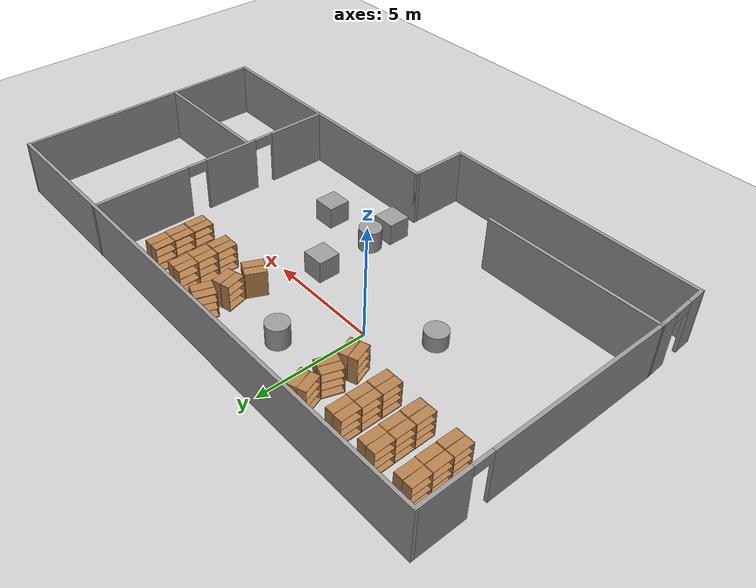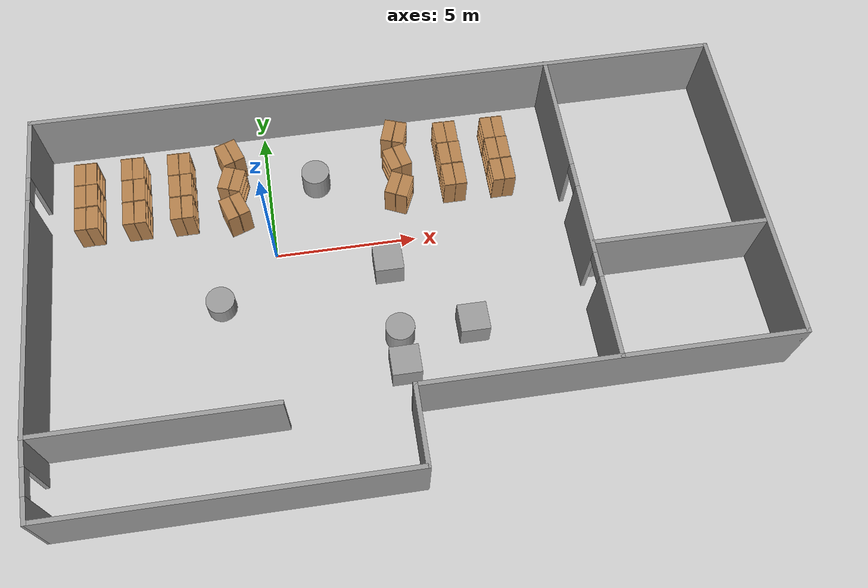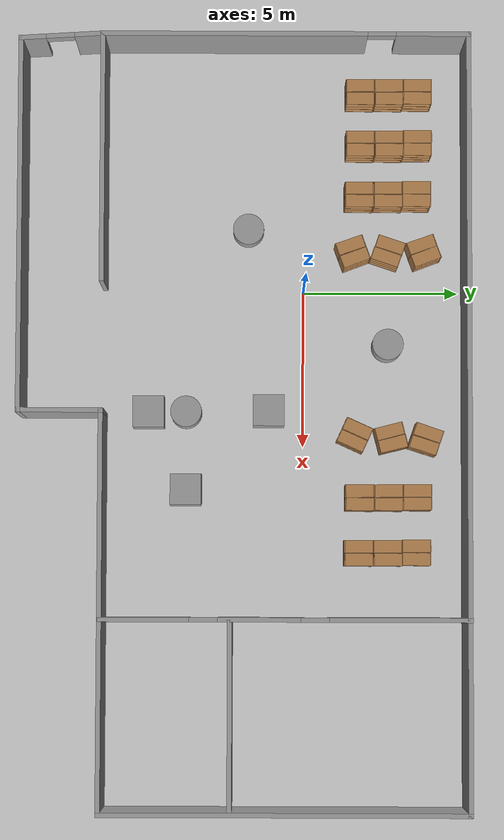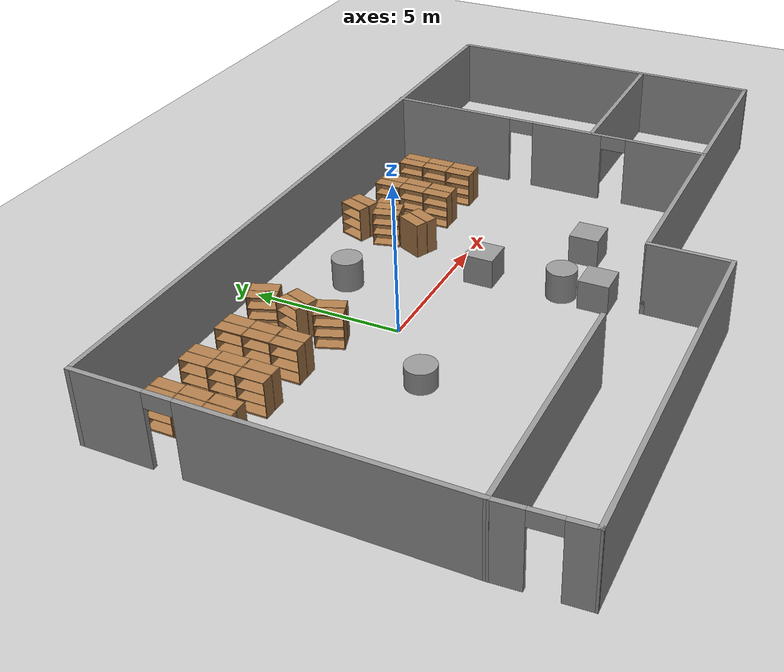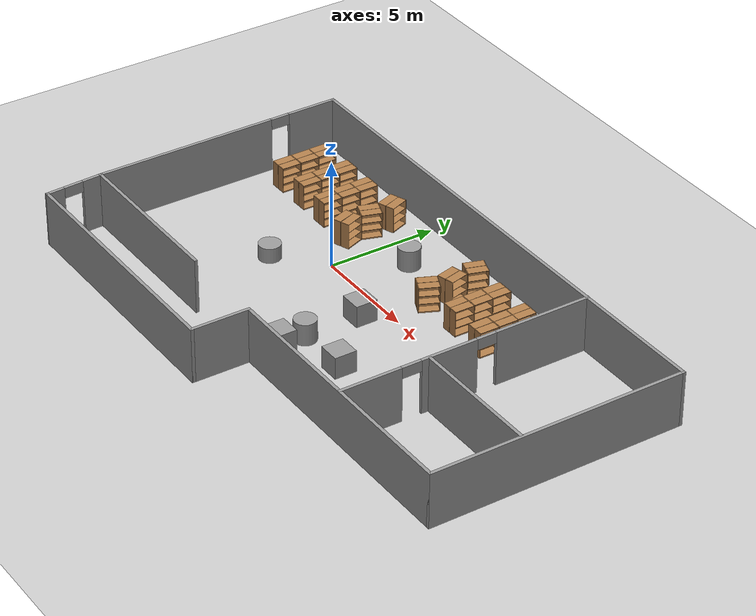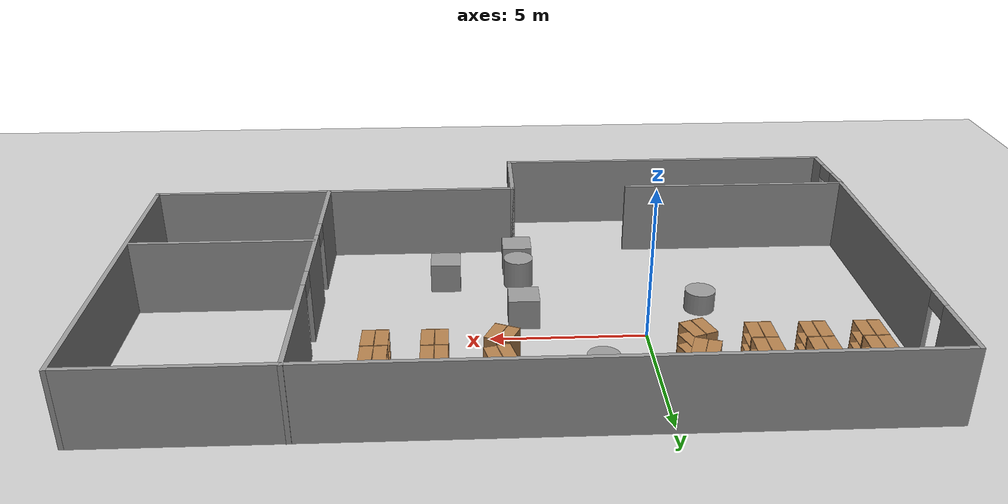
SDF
<sdf version="1.7">
 <world name="default">
  <light name="sun" type="directional">
   <pose>0 0 10 0 -0 0</pose>
   <diffuse>0.8 0.8 0.8 1</diffuse>
   <specular>0.2 0.2 0.2 1</specular>
   <attenuation>
    <range>1000</range>
    <constant>0.9</constant>
    <linear>0.01</linear>
    <quadratic>0.001</quadratic>
   </attenuation>
   <direction>-0.5 0.1 -0.9</direction>
   <spot><inner_angle>0</inner_angle><outer_angle>0</outer_angle><falloff>0</falloff></spot>
  </light>
  <gravity>0 0 -9.8</gravity>
  <magnetic_field>6e-06 2.3e-05 -4.2e-05</magnetic_field>
  <atmosphere type="adiabatic"/>
  <physics type="ode">
   <max_step_size>0.001</max_step_size>
   <real_time_factor>1</real_time_factor>
   <real_time_update_rate>1000</real_time_update_rate>
  </physics>
  <scene><ambient>0.4 0.4 0.4 1</ambient><background>0.7 0.7 0.7 1</background><shadows>1</shadows></scene>
  <spherical_coordinates>
   <surface_model>EARTH_WGS84</surface_model>
   <latitude_deg>0</latitude_deg>
   <longitude_deg>0</longitude_deg>
   <elevation>0</elevation>
   <heading_deg>0</heading_deg>
  </spherical_coordinates>
  <model name="booookshelf">
   <model name="bookshelf">
    <static>1</static>
    <link name="link">
     <inertial><mass>1</mass></inertial>
     <collision name="back">
      <pose>0 0.005 0.6 0 -0 0</pose>
      <geometry><box><size>0.9 0.01 1.2</size></box></geometry>
     </collision>
     <visual name="visual1">
      <pose>0 0.005 0.6 0 -0 0</pose>
      <geometry><box><size>0.9 0.01 1.2</size></box></geometry>
      <material>
       <script><uri>file://media/materials/scripts/gazebo.material</uri><name>Gazebo/Wood</name></script>
      </material>
     </visual>
     <collision name="left_side">
      <pose>0.45 -0.195 0.6 0 -0 0</pose>
      <geometry><box><size>0.02 0.4 1.2</size></box></geometry>
     </collision>
     <visual name="visual2">
      <pose>0.45 -0.195 0.6 0 -0 0</pose>
      <geometry><box><size>0.02 0.4 1.2</size></box></geometry>
      <material>
       <script><uri>file://media/materials/scripts/gazebo.material</uri><name>Gazebo/Wood</name></script>
      </material>
     </visual>
     <collision name="right_side">
      <pose>-0.45 -0.195 0.6 0 -0 0</pose>
      <geometry><box><size>0.02 0.4 1.2</size></box></geometry>
     </collision>
     <visual name="visual3">
      <pose>-0.45 -0.195 0.6 0 -0 0</pose>
      <geometry><box><size>0.02 0.4 1.2</size></box></geometry>
      <material>
       <script><uri>file://media/materials/scripts/gazebo.material</uri><name>Gazebo/Wood</name></script>
      </material>
     </visual>
     <collision name="bottom">
      <pose>0 -0.195 0.03 0 -0 0</pose>
      <geometry><box><size>0.88 0.4 0.06</size></box></geometry>
     </collision>
     <visual name="visual4">
      <pose>0 -0.195 0.03 0 -0 0</pose>
      <geometry><box><size>0.88 0.4 0.06</size></box></geometry>
      <material>
       <script><uri>file://media/materials/scripts/gazebo.material</uri><name>Gazebo/Wood</name></script>
      </material>
     </visual>
     <collision name="top">
      <pose>0 -0.195 1.19 0 -0 0</pose>
      <geometry><box><size>0.88 0.4 0.02</size></box></geometry>
     </collision>
     <visual name="visual5">
      <pose>0 -0.195 1.19 0 -0 0</pose>
      <geometry><box><size>0.88 0.4 0.02</size></box></geometry>
      <material>
       <script><uri>file://media/materials/scripts/gazebo.material</uri><name>Gazebo/Wood</name></script>
      </material>
     </visual>
     <collision name="low_shelf">
      <pose>0 -0.195 0.43 0 -0 0</pose>
      <geometry><box><size>0.88 0.4 0.02</size></box></geometry>
     </collision>
     <visual name="visual6">
      <pose>0 -0.195 0.43 0 -0 0</pose>
      <geometry><box><size>0.88 0.4 0.02</size></box></geometry>
      <material>
       <script><uri>file://media/materials/scripts/gazebo.material</uri><name>Gazebo/Wood</name></script>
      </material>
     </visual>
     <collision name="high_shelf">
      <pose>0 -0.195 0.8 0 -0 0</pose>
      <geometry><box><size>0.88 0.4 0.02</size></box></geometry>
     </collision>
     <visual name="visual7">
      <pose>0 -0.195 0.8 0 -0 0</pose>
      <geometry><box><size>0.88 0.4 0.02</size></box></geometry>
      <material>
       <script><uri>file://media/materials/scripts/gazebo.material</uri><name>Gazebo/Wood</name></script>
      </material>
     </visual>
    </link>
    <pose>-0.009683 0.000159 0 0 0 -1.56493</pose>
   </model>
   <model name="bookshelf_clone">
    <static>1</static>
    <link name="link">
     <inertial><mass>1</mass></inertial>
     <collision name="back">
      <pose>0 0.005 0.6 0 -0 0</pose>
      <geometry><box><size>0.9 0.01 1.2</size></box></geometry>
     </collision>
     <visual name="visual1">
      <pose>0 0.005 0.6 0 -0 0</pose>
      <geometry><box><size>0.9 0.01 1.2</size></box></geometry>
      <material>
       <script><uri>file://media/materials/scripts/gazebo.material</uri><name>Gazebo/Wood</name></script>
      </material>
     </visual>
     <collision name="left_side">
      <pose>0.45 -0.195 0.6 0 -0 0</pose>
      <geometry><box><size>0.02 0.4 1.2</size></box></geometry>
     </collision>
     <visual name="visual2">
      <pose>0.45 -0.195 0.6 0 -0 0</pose>
      <geometry><box><size>0.02 0.4 1.2</size></box></geometry>
      <material>
       <script><uri>file://media/materials/scripts/gazebo.material</uri><name>Gazebo/Wood</name></script>
      </material>
     </visual>
     <collision name="right_side">
      <pose>-0.45 -0.195 0.6 0 -0 0</pose>
      <geometry><box><size>0.02 0.4 1.2</size></box></geometry>
     </collision>
     <visual name="visual3">
      <pose>-0.45 -0.195 0.6 0 -0 0</pose>
      <geometry><box><size>0.02 0.4 1.2</size></box></geometry>
      <material>
       <script><uri>file://media/materials/scripts/gazebo.material</uri><name>Gazebo/Wood</name></script>
      </material>
     </visual>
     <collision name="bottom">
      <pose>0 -0.195 0.03 0 -0 0</pose>
      <geometry><box><size>0.88 0.4 0.06</size></box></geometry>
     </collision>
     <visual name="visual4">
      <pose>0 -0.195 0.03 0 -0 0</pose>
      <geometry><box><size>0.88 0.4 0.06</size></box></geometry>
      <material>
       <script><uri>file://media/materials/scripts/gazebo.material</uri><name>Gazebo/Wood</name></script>
      </material>
     </visual>
     <collision name="top">
      <pose>0 -0.195 1.19 0 -0 0</pose>
      <geometry><box><size>0.88 0.4 0.02</size></box></geometry>
     </collision>
     <visual name="visual5">
      <pose>0 -0.195 1.19 0 -0 0</pose>
      <geometry><box><size>0.88 0.4 0.02</size></box></geometry>
      <material>
       <script><uri>file://media/materials/scripts/gazebo.material</uri><name>Gazebo/Wood</name></script>
      </material>
     </visual>
     <collision name="low_shelf">
      <pose>0 -0.195 0.43 0 -0 0</pose>
      <geometry><box><size>0.88 0.4 0.02</size></box></geometry>
     </collision>
     <visual name="visual6">
      <pose>0 -0.195 0.43 0 -0 0</pose>
      <geometry><box><size>0.88 0.4 0.02</size></box></geometry>
      <material>
       <script><uri>file://media/materials/scripts/gazebo.material</uri><name>Gazebo/Wood</name></script>
      </material>
     </visual>
     <collision name="high_shelf">
      <pose>0 -0.195 0.8 0 -0 0</pose>
      <geometry><box><size>0.88 0.4 0.02</size></box></geometry>
     </collision>
     <visual name="visual7">
      <pose>0 -0.195 0.8 0 -0 0</pose>
      <geometry><box><size>0.88 0.4 0.02</size></box></geometry>
      <material>
       <script><uri>file://media/materials/scripts/gazebo.material</uri><name>Gazebo/Wood</name></script>
      </material>
     </visual>
    </link>
    <pose>-0.008394 -0.921313 0 0 0 -1.56493</pose>
   </model>
   <model name="bookshelf_clone_0">
    <static>1</static>
    <link name="link">
     <inertial><mass>1</mass></inertial>
     <collision name="back">
      <pose>0 0.005 0.6 0 -0 0</pose>
      <geometry><box><size>0.9 0.01 1.2</size></box></geometry>
     </collision>
     <visual name="visual1">
      <pose>0 0.005 0.6 0 -0 0</pose>
      <geometry><box><size>0.9 0.01 1.2</size></box></geometry>
      <material>
       <script><uri>file://media/materials/scripts/gazebo.material</uri><name>Gazebo/Wood</name></script>
      </material>
     </visual>
     <collision name="left_side">
      <pose>0.45 -0.195 0.6 0 -0 0</pose>
      <geometry><box><size>0.02 0.4 1.2</size></box></geometry>
     </collision>
     <visual name="visual2">
      <pose>0.45 -0.195 0.6 0 -0 0</pose>
      <geometry><box><size>0.02 0.4 1.2</size></box></geometry>
      <material>
       <script><uri>file://media/materials/scripts/gazebo.material</uri><name>Gazebo/Wood</name></script>
      </material>
     </visual>
     <collision name="right_side">
      <pose>-0.45 -0.195 0.6 0 -0 0</pose>
      <geometry><box><size>0.02 0.4 1.2</size></box></geometry>
     </collision>
     <visual name="visual3">
      <pose>-0.45 -0.195 0.6 0 -0 0</pose>
      <geometry><box><size>0.02 0.4 1.2</size></box></geometry>
      <material>
       <script><uri>file://media/materials/scripts/gazebo.material</uri><name>Gazebo/Wood</name></script>
      </material>
     </visual>
     <collision name="bottom">
      <pose>0 -0.195 0.03 0 -0 0</pose>
      <geometry><box><size>0.88 0.4 0.06</size></box></geometry>
     </collision>
     <visual name="visual4">
      <pose>0 -0.195 0.03 0 -0 0</pose>
      <geometry><box><size>0.88 0.4 0.06</size></box></geometry>
      <material>
       <script><uri>file://media/materials/scripts/gazebo.material</uri><name>Gazebo/Wood</name></script>
      </material>
     </visual>
     <collision name="top">
      <pose>0 -0.195 1.19 0 -0 0</pose>
      <geometry><box><size>0.88 0.4 0.02</size></box></geometry>
     </collision>
     <visual name="visual5">
      <pose>0 -0.195 1.19 0 -0 0</pose>
      <geometry><box><size>0.88 0.4 0.02</size></box></geometry>
      <material>
       <script><uri>file://media/materials/scripts/gazebo.material</uri><name>Gazebo/Wood</name></script>
      </material>
     </visual>
     <collision name="low_shelf">
      <pose>0 -0.195 0.43 0 -0 0</pose>
      <geometry><box><size>0.88 0.4 0.02</size></box></geometry>
     </collision>
     <visual name="visual6">
      <pose>0 -0.195 0.43 0 -0 0</pose>
      <geometry><box><size>0.88 0.4 0.02</size></box></geometry>
      <material>
       <script><uri>file://media/materials/scripts/gazebo.material</uri><name>Gazebo/Wood</name></script>
      </material>
     </visual>
     <collision name="high_shelf">
      <pose>0 -0.195 0.8 0 -0 0</pose>
      <geometry><box><size>0.88 0.4 0.02</size></box></geometry>
     </collision>
     <visual name="visual7">
      <pose>0 -0.195 0.8 0 -0 0</pose>
      <geometry><box><size>0.88 0.4 0.02</size></box></geometry>
      <material>
       <script><uri>file://media/materials/scripts/gazebo.material</uri><name>Gazebo/Wood</name></script>
      </material>
     </visual>
    </link>
    <pose>-0.020188 0.9173 0 0 0 -1.56493</pose>
   </model>
   <model name="bookshelf_clone_1">
    <static>1</static>
    <link name="link">
     <inertial><mass>1</mass></inertial>
     <collision name="back">
      <pose>0 0.005 0.6 0 -0 0</pose>
      <geometry><box><size>0.9 0.01 1.2</size></box></geometry>
     </collision>
     <visual name="visual1">
      <pose>0 0.005 0.6 0 -0 0</pose>
      <geometry><box><size>0.9 0.01 1.2</size></box></geometry>
      <material>
       <script><uri>file://media/materials/scripts/gazebo.material</uri><name>Gazebo/Wood</name></script>
      </material>
     </visual>
     <collision name="left_side">
      <pose>0.45 -0.195 0.6 0 -0 0</pose>
      <geometry><box><size>0.02 0.4 1.2</size></box></geometry>
     </collision>
     <visual name="visual2">
      <pose>0.45 -0.195 0.6 0 -0 0</pose>
      <geometry><box><size>0.02 0.4 1.2</size></box></geometry>
      <material>
       <script><uri>file://media/materials/scripts/gazebo.material</uri><name>Gazebo/Wood</name></script>
      </material>
     </visual>
     <collision name="right_side">
      <pose>-0.45 -0.195 0.6 0 -0 0</pose>
      <geometry><box><size>0.02 0.4 1.2</size></box></geometry>
     </collision>
     <visual name="visual3">
      <pose>-0.45 -0.195 0.6 0 -0 0</pose>
      <geometry><box><size>0.02 0.4 1.2</size></box></geometry>
      <material>
       <script><uri>file://media/materials/scripts/gazebo.material</uri><name>Gazebo/Wood</name></script>
      </material>
     </visual>
     <collision name="bottom">
      <pose>0 -0.195 0.03 0 -0 0</pose>
      <geometry><box><size>0.88 0.4 0.06</size></box></geometry>
     </collision>
     <visual name="visual4">
      <pose>0 -0.195 0.03 0 -0 0</pose>
      <geometry><box><size>0.88 0.4 0.06</size></box></geometry>
      <material>
       <script><uri>file://media/materials/scripts/gazebo.material</uri><name>Gazebo/Wood</name></script>
      </material>
     </visual>
     <collision name="top">
      <pose>0 -0.195 1.19 0 -0 0</pose>
      <geometry><box><size>0.88 0.4 0.02</size></box></geometry>
     </collision>
     <visual name="visual5">
      <pose>0 -0.195 1.19 0 -0 0</pose>
      <geometry><box><size>0.88 0.4 0.02</size></box></geometry>
      <material>
       <script><uri>file://media/materials/scripts/gazebo.material</uri><name>Gazebo/Wood</name></script>
      </material>
     </visual>
     <collision name="low_shelf">
      <pose>0 -0.195 0.43 0 -0 0</pose>
      <geometry><box><size>0.88 0.4 0.02</size></box></geometry>
     </collision>
     <visual name="visual6">
      <pose>0 -0.195 0.43 0 -0 0</pose>
      <geometry><box><size>0.88 0.4 0.02</size></box></geometry>
      <material>
       <script><uri>file://media/materials/scripts/gazebo.material</uri><name>Gazebo/Wood</name></script>
      </material>
     </visual>
     <collision name="high_shelf">
      <pose>0 -0.195 0.8 0 -0 0</pose>
      <geometry><box><size>0.88 0.4 0.02</size></box></geometry>
     </collision>
     <visual name="visual7">
      <pose>0 -0.195 0.8 0 -0 0</pose>
      <geometry><box><size>0.88 0.4 0.02</size></box></geometry>
      <material>
       <script><uri>file://media/materials/scripts/gazebo.material</uri><name>Gazebo/Wood</name></script>
      </material>
     </visual>
    </link>
    <pose>0.019389 -0.918185 0 0 -0 1.55949</pose>
   </model>
   <model name="bookshelf_clone_1_clone">
    <static>1</static>
    <link name="link">
     <inertial><mass>1</mass></inertial>
     <collision name="back">
      <pose>0 0.005 0.6 0 -0 0</pose>
      <geometry><box><size>0.9 0.01 1.2</size></box></geometry>
     </collision>
     <visual name="visual1">
      <pose>0 0.005 0.6 0 -0 0</pose>
      <geometry><box><size>0.9 0.01 1.2</size></box></geometry>
      <material>
       <script><uri>file://media/materials/scripts/gazebo.material</uri><name>Gazebo/Wood</name></script>
      </material>
     </visual>
     <collision name="left_side">
      <pose>0.45 -0.195 0.6 0 -0 0</pose>
      <geometry><box><size>0.02 0.4 1.2</size></box></geometry>
     </collision>
     <visual name="visual2">
      <pose>0.45 -0.195 0.6 0 -0 0</pose>
      <geometry><box><size>0.02 0.4 1.2</size></box></geometry>
      <material>
       <script><uri>file://media/materials/scripts/gazebo.material</uri><name>Gazebo/Wood</name></script>
      </material>
     </visual>
     <collision name="right_side">
      <pose>-0.45 -0.195 0.6 0 -0 0</pose>
      <geometry><box><size>0.02 0.4 1.2</size></box></geometry>
     </collision>
     <visual name="visual3">
      <pose>-0.45 -0.195 0.6 0 -0 0</pose>
      <geometry><box><size>0.02 0.4 1.2</size></box></geometry>
      <material>
       <script><uri>file://media/materials/scripts/gazebo.material</uri><name>Gazebo/Wood</name></script>
      </material>
     </visual>
     <collision name="bottom">
      <pose>0 -0.195 0.03 0 -0 0</pose>
      <geometry><box><size>0.88 0.4 0.06</size></box></geometry>
     </collision>
     <visual name="visual4">
      <pose>0 -0.195 0.03 0 -0 0</pose>
      <geometry><box><size>0.88 0.4 0.06</size></box></geometry>
      <material>
       <script><uri>file://media/materials/scripts/gazebo.material</uri><name>Gazebo/Wood</name></script>
      </material>
     </visual>
     <collision name="top">
      <pose>0 -0.195 1.19 0 -0 0</pose>
      <geometry><box><size>0.88 0.4 0.02</size></box></geometry>
     </collision>
     <visual name="visual5">
      <pose>0 -0.195 1.19 0 -0 0</pose>
      <geometry><box><size>0.88 0.4 0.02</size></box></geometry>
      <material>
       <script><uri>file://media/materials/scripts/gazebo.material</uri><name>Gazebo/Wood</name></script>
      </material>
     </visual>
     <collision name="low_shelf">
      <pose>0 -0.195 0.43 0 -0 0</pose>
      <geometry><box><size>0.88 0.4 0.02</size></box></geometry>
     </collision>
     <visual name="visual6">
      <pose>0 -0.195 0.43 0 -0 0</pose>
      <geometry><box><size>0.88 0.4 0.02</size></box></geometry>
      <material>
       <script><uri>file://media/materials/scripts/gazebo.material</uri><name>Gazebo/Wood</name></script>
      </material>
     </visual>
     <collision name="high_shelf">
      <pose>0 -0.195 0.8 0 -0 0</pose>
      <geometry><box><size>0.88 0.4 0.02</size></box></geometry>
     </collision>
     <visual name="visual7">
      <pose>0 -0.195 0.8 0 -0 0</pose>
      <geometry><box><size>0.88 0.4 0.02</size></box></geometry>
      <material>
       <script><uri>file://media/materials/scripts/gazebo.material</uri><name>Gazebo/Wood</name></script>
      </material>
     </visual>
    </link>
    <pose>0.016888 0.010932 0 0 -0 1.55949</pose>
   </model>
   <model name="bookshelf_clone_1_clone_0">
    <static>1</static>
    <link name="link">
     <inertial><mass>1</mass></inertial>
     <collision name="back">
      <pose>0 0.005 0.6 0 -0 0</pose>
      <geometry><box><size>0.9 0.01 1.2</size></box></geometry>
     </collision>
     <visual name="visual1">
      <pose>0 0.005 0.6 0 -0 0</pose>
      <geometry><box><size>0.9 0.01 1.2</size></box></geometry>
      <material>
       <script><uri>file://media/materials/scripts/gazebo.material</uri><name>Gazebo/Wood</name></script>
      </material>
     </visual>
     <collision name="left_side">
      <pose>0.45 -0.195 0.6 0 -0 0</pose>
      <geometry><box><size>0.02 0.4 1.2</size></box></geometry>
     </collision>
     <visual name="visual2">
      <pose>0.45 -0.195 0.6 0 -0 0</pose>
      <geometry><box><size>0.02 0.4 1.2</size></box></geometry>
      <material>
       <script><uri>file://media/materials/scripts/gazebo.material</uri><name>Gazebo/Wood</name></script>
      </material>
     </visual>
     <collision name="right_side">
      <pose>-0.45 -0.195 0.6 0 -0 0</pose>
      <geometry><box><size>0.02 0.4 1.2</size></box></geometry>
     </collision>
     <visual name="visual3">
      <pose>-0.45 -0.195 0.6 0 -0 0</pose>
      <geometry><box><size>0.02 0.4 1.2</size></box></geometry>
      <material>
       <script><uri>file://media/materials/scripts/gazebo.material</uri><name>Gazebo/Wood</name></script>
      </material>
     </visual>
     <collision name="bottom">
      <pose>0 -0.195 0.03 0 -0 0</pose>
      <geometry><box><size>0.88 0.4 0.06</size></box></geometry>
     </collision>
     <visual name="visual4">
      <pose>0 -0.195 0.03 0 -0 0</pose>
      <geometry><box><size>0.88 0.4 0.06</size></box></geometry>
      <material>
       <script><uri>file://media/materials/scripts/gazebo.material</uri><name>Gazebo/Wood</name></script>
      </material>
     </visual>
     <collision name="top">
      <pose>0 -0.195 1.19 0 -0 0</pose>
      <geometry><box><size>0.88 0.4 0.02</size></box></geometry>
     </collision>
     <visual name="visual5">
      <pose>0 -0.195 1.19 0 -0 0</pose>
      <geometry><box><size>0.88 0.4 0.02</size></box></geometry>
      <material>
       <script><uri>file://media/materials/scripts/gazebo.material</uri><name>Gazebo/Wood</name></script>
      </material>
     </visual>
     <collision name="low_shelf">
      <pose>0 -0.195 0.43 0 -0 0</pose>
      <geometry><box><size>0.88 0.4 0.02</size></box></geometry>
     </collision>
     <visual name="visual6">
      <pose>0 -0.195 0.43 0 -0 0</pose>
      <geometry><box><size>0.88 0.4 0.02</size></box></geometry>
      <material>
       <script><uri>file://media/materials/scripts/gazebo.material</uri><name>Gazebo/Wood</name></script>
      </material>
     </visual>
     <collision name="high_shelf">
      <pose>0 -0.195 0.8 0 -0 0</pose>
      <geometry><box><size>0.88 0.4 0.02</size></box></geometry>
     </collision>
     <visual name="visual7">
      <pose>0 -0.195 0.8 0 -0 0</pose>
      <geometry><box><size>0.88 0.4 0.02</size></box></geometry>
      <material>
       <script><uri>file://media/materials/scripts/gazebo.material</uri><name>Gazebo/Wood</name></script>
      </material>
     </visual>
    </link>
    <pose>0.001995 0.911101 0 0 -0 1.55949</pose>
   </model>
   <static>0</static>
   <pose>-3.08471 2.7047 0 0 -0 0</pose>
  </model>
  <model name="booookshelf_0">
   <model name="bookshelf">
    <static>1</static>
    <link name="link">
     <inertial><mass>1</mass></inertial>
     <collision name="back">
      <pose>0 0.005 0.6 0 -0 0</pose>
      <geometry><box><size>0.9 0.01 1.2</size></box></geometry>
     </collision>
     <visual name="visual1">
      <pose>0 0.005 0.6 0 -0 0</pose>
      <geometry><box><size>0.9 0.01 1.2</size></box></geometry>
      <material>
       <script><uri>file://media/materials/scripts/gazebo.material</uri><name>Gazebo/Wood</name></script>
      </material>
     </visual>
     <collision name="left_side">
      <pose>0.45 -0.195 0.6 0 -0 0</pose>
      <geometry><box><size>0.02 0.4 1.2</size></box></geometry>
     </collision>
     <visual name="visual2">
      <pose>0.45 -0.195 0.6 0 -0 0</pose>
      <geometry><box><size>0.02 0.4 1.2</size></box></geometry>
      <material>
       <script><uri>file://media/materials/scripts/gazebo.material</uri><name>Gazebo/Wood</name></script>
      </material>
     </visual>
     <collision name="right_side">
      <pose>-0.45 -0.195 0.6 0 -0 0</pose>
      <geometry><box><size>0.02 0.4 1.2</size></box></geometry>
     </collision>
     <visual name="visual3">
      <pose>-0.45 -0.195 0.6 0 -0 0</pose>
      <geometry><box><size>0.02 0.4 1.2</size></box></geometry>
      <material>
       <script><uri>file://media/materials/scripts/gazebo.material</uri><name>Gazebo/Wood</name></script>
      </material>
     </visual>
     <collision name="bottom">
      <pose>0 -0.195 0.03 0 -0 0</pose>
      <geometry><box><size>0.88 0.4 0.06</size></box></geometry>
     </collision>
     <visual name="visual4">
      <pose>0 -0.195 0.03 0 -0 0</pose>
      <geometry><box><size>0.88 0.4 0.06</size></box></geometry>
      <material>
       <script><uri>file://media/materials/scripts/gazebo.material</uri><name>Gazebo/Wood</name></script>
      </material>
     </visual>
     <collision name="top">
      <pose>0 -0.195 1.19 0 -0 0</pose>
      <geometry><box><size>0.88 0.4 0.02</size></box></geometry>
     </collision>
     <visual name="visual5">
      <pose>0 -0.195 1.19 0 -0 0</pose>
      <geometry><box><size>0.88 0.4 0.02</size></box></geometry>
      <material>
       <script><uri>file://media/materials/scripts/gazebo.material</uri><name>Gazebo/Wood</name></script>
      </material>
     </visual>
     <collision name="low_shelf">
      <pose>0 -0.195 0.43 0 -0 0</pose>
      <geometry><box><size>0.88 0.4 0.02</size></box></geometry>
     </collision>
     <visual name="visual6">
      <pose>0 -0.195 0.43 0 -0 0</pose>
      <geometry><box><size>0.88 0.4 0.02</size></box></geometry>
      <material>
       <script><uri>file://media/materials/scripts/gazebo.material</uri><name>Gazebo/Wood</name></script>
      </material>
     </visual>
     <collision name="high_shelf">
      <pose>0 -0.195 0.8 0 -0 0</pose>
      <geometry><box><size>0.88 0.4 0.02</size></box></geometry>
     </collision>
     <visual name="visual7">
      <pose>0 -0.195 0.8 0 -0 0</pose>
      <geometry><box><size>0.88 0.4 0.02</size></box></geometry>
      <material>
       <script><uri>file://media/materials/scripts/gazebo.material</uri><name>Gazebo/Wood</name></script>
      </material>
     </visual>
    </link>
    <pose>-0.009683 0.000159 0 0 0 -1.56493</pose>
   </model>
   <model name="bookshelf_clone">
    <static>1</static>
    <link name="link">
     <inertial><mass>1</mass></inertial>
     <collision name="back">
      <pose>0 0.005 0.6 0 -0 0</pose>
      <geometry><box><size>0.9 0.01 1.2</size></box></geometry>
     </collision>
     <visual name="visual1">
      <pose>0 0.005 0.6 0 -0 0</pose>
      <geometry><box><size>0.9 0.01 1.2</size></box></geometry>
      <material>
       <script><uri>file://media/materials/scripts/gazebo.material</uri><name>Gazebo/Wood</name></script>
      </material>
     </visual>
     <collision name="left_side">
      <pose>0.45 -0.195 0.6 0 -0 0</pose>
      <geometry><box><size>0.02 0.4 1.2</size></box></geometry>
     </collision>
     <visual name="visual2">
      <pose>0.45 -0.195 0.6 0 -0 0</pose>
      <geometry><box><size>0.02 0.4 1.2</size></box></geometry>
      <material>
       <script><uri>file://media/materials/scripts/gazebo.material</uri><name>Gazebo/Wood</name></script>
      </material>
     </visual>
     <collision name="right_side">
      <pose>-0.45 -0.195 0.6 0 -0 0</pose>
      <geometry><box><size>0.02 0.4 1.2</size></box></geometry>
     </collision>
     <visual name="visual3">
      <pose>-0.45 -0.195 0.6 0 -0 0</pose>
      <geometry><box><size>0.02 0.4 1.2</size></box></geometry>
      <material>
       <script><uri>file://media/materials/scripts/gazebo.material</uri><name>Gazebo/Wood</name></script>
      </material>
     </visual>
     <collision name="bottom">
      <pose>0 -0.195 0.03 0 -0 0</pose>
      <geometry><box><size>0.88 0.4 0.06</size></box></geometry>
     </collision>
     <visual name="visual4">
      <pose>0 -0.195 0.03 0 -0 0</pose>
      <geometry><box><size>0.88 0.4 0.06</size></box></geometry>
      <material>
       <script><uri>file://media/materials/scripts/gazebo.material</uri><name>Gazebo/Wood</name></script>
      </material>
     </visual>
     <collision name="top">
      <pose>0 -0.195 1.19 0 -0 0</pose>
      <geometry><box><size>0.88 0.4 0.02</size></box></geometry>
     </collision>
     <visual name="visual5">
      <pose>0 -0.195 1.19 0 -0 0</pose>
      <geometry><box><size>0.88 0.4 0.02</size></box></geometry>
      <material>
       <script><uri>file://media/materials/scripts/gazebo.material</uri><name>Gazebo/Wood</name></script>
      </material>
     </visual>
     <collision name="low_shelf">
      <pose>0 -0.195 0.43 0 -0 0</pose>
      <geometry><box><size>0.88 0.4 0.02</size></box></geometry>
     </collision>
     <visual name="visual6">
      <pose>0 -0.195 0.43 0 -0 0</pose>
      <geometry><box><size>0.88 0.4 0.02</size></box></geometry>
      <material>
       <script><uri>file://media/materials/scripts/gazebo.material</uri><name>Gazebo/Wood</name></script>
      </material>
     </visual>
     <collision name="high_shelf">
      <pose>0 -0.195 0.8 0 -0 0</pose>
      <geometry><box><size>0.88 0.4 0.02</size></box></geometry>
     </collision>
     <visual name="visual7">
      <pose>0 -0.195 0.8 0 -0 0</pose>
      <geometry><box><size>0.88 0.4 0.02</size></box></geometry>
      <material>
       <script><uri>file://media/materials/scripts/gazebo.material</uri><name>Gazebo/Wood</name></script>
      </material>
     </visual>
    </link>
    <pose>-0.008394 -0.921313 0 0 0 -1.56493</pose>
   </model>
   <model name="bookshelf_clone_0">
    <static>1</static>
    <link name="link">
     <inertial><mass>1</mass></inertial>
     <collision name="back">
      <pose>0 0.005 0.6 0 -0 0</pose>
      <geometry><box><size>0.9 0.01 1.2</size></box></geometry>
     </collision>
     <visual name="visual1">
      <pose>0 0.005 0.6 0 -0 0</pose>
      <geometry><box><size>0.9 0.01 1.2</size></box></geometry>
      <material>
       <script><uri>file://media/materials/scripts/gazebo.material</uri><name>Gazebo/Wood</name></script>
      </material>
     </visual>
     <collision name="left_side">
      <pose>0.45 -0.195 0.6 0 -0 0</pose>
      <geometry><box><size>0.02 0.4 1.2</size></box></geometry>
     </collision>
     <visual name="visual2">
      <pose>0.45 -0.195 0.6 0 -0 0</pose>
      <geometry><box><size>0.02 0.4 1.2</size></box></geometry>
      <material>
       <script><uri>file://media/materials/scripts/gazebo.material</uri><name>Gazebo/Wood</name></script>
      </material>
     </visual>
     <collision name="right_side">
      <pose>-0.45 -0.195 0.6 0 -0 0</pose>
      <geometry><box><size>0.02 0.4 1.2</size></box></geometry>
     </collision>
     <visual name="visual3">
      <pose>-0.45 -0.195 0.6 0 -0 0</pose>
      <geometry><box><size>0.02 0.4 1.2</size></box></geometry>
      <material>
       <script><uri>file://media/materials/scripts/gazebo.material</uri><name>Gazebo/Wood</name></script>
      </material>
     </visual>
     <collision name="bottom">
      <pose>0 -0.195 0.03 0 -0 0</pose>
      <geometry><box><size>0.88 0.4 0.06</size></box></geometry>
     </collision>
     <visual name="visual4">
      <pose>0 -0.195 0.03 0 -0 0</pose>
      <geometry><box><size>0.88 0.4 0.06</size></box></geometry>
      <material>
       <script><uri>file://media/materials/scripts/gazebo.material</uri><name>Gazebo/Wood</name></script>
      </material>
     </visual>
     <collision name="top">
      <pose>0 -0.195 1.19 0 -0 0</pose>
      <geometry><box><size>0.88 0.4 0.02</size></box></geometry>
     </collision>
     <visual name="visual5">
      <pose>0 -0.195 1.19 0 -0 0</pose>
      <geometry><box><size>0.88 0.4 0.02</size></box></geometry>
      <material>
       <script><uri>file://media/materials/scripts/gazebo.material</uri><name>Gazebo/Wood</name></script>
      </material>
     </visual>
     <collision name="low_shelf">
      <pose>0 -0.195 0.43 0 -0 0</pose>
      <geometry><box><size>0.88 0.4 0.02</size></box></geometry>
     </collision>
     <visual name="visual6">
      <pose>0 -0.195 0.43 0 -0 0</pose>
      <geometry><box><size>0.88 0.4 0.02</size></box></geometry>
      <material>
       <script><uri>file://media/materials/scripts/gazebo.material</uri><name>Gazebo/Wood</name></script>
      </material>
     </visual>
     <collision name="high_shelf">
      <pose>0 -0.195 0.8 0 -0 0</pose>
      <geometry><box><size>0.88 0.4 0.02</size></box></geometry>
     </collision>
     <visual name="visual7">
      <pose>0 -0.195 0.8 0 -0 0</pose>
      <geometry><box><size>0.88 0.4 0.02</size></box></geometry>
      <material>
       <script><uri>file://media/materials/scripts/gazebo.material</uri><name>Gazebo/Wood</name></script>
      </material>
     </visual>
    </link>
    <pose>-0.020188 0.9173 0 0 0 -1.56493</pose>
   </model>
   <model name="bookshelf_clone_1">
    <static>1</static>
    <link name="link">
     <inertial><mass>1</mass></inertial>
     <collision name="back">
      <pose>0 0.005 0.6 0 -0 0</pose>
      <geometry><box><size>0.9 0.01 1.2</size></box></geometry>
     </collision>
     <visual name="visual1">
      <pose>0 0.005 0.6 0 -0 0</pose>
      <geometry><box><size>0.9 0.01 1.2</size></box></geometry>
      <material>
       <script><uri>file://media/materials/scripts/gazebo.material</uri><name>Gazebo/Wood</name></script>
      </material>
     </visual>
     <collision name="left_side">
      <pose>0.45 -0.195 0.6 0 -0 0</pose>
      <geometry><box><size>0.02 0.4 1.2</size></box></geometry>
     </collision>
     <visual name="visual2">
      <pose>0.45 -0.195 0.6 0 -0 0</pose>
      <geometry><box><size>0.02 0.4 1.2</size></box></geometry>
      <material>
       <script><uri>file://media/materials/scripts/gazebo.material</uri><name>Gazebo/Wood</name></script>
      </material>
     </visual>
     <collision name="right_side">
      <pose>-0.45 -0.195 0.6 0 -0 0</pose>
      <geometry><box><size>0.02 0.4 1.2</size></box></geometry>
     </collision>
     <visual name="visual3">
      <pose>-0.45 -0.195 0.6 0 -0 0</pose>
      <geometry><box><size>0.02 0.4 1.2</size></box></geometry>
      <material>
       <script><uri>file://media/materials/scripts/gazebo.material</uri><name>Gazebo/Wood</name></script>
      </material>
     </visual>
     <collision name="bottom">
      <pose>0 -0.195 0.03 0 -0 0</pose>
      <geometry><box><size>0.88 0.4 0.06</size></box></geometry>
     </collision>
     <visual name="visual4">
      <pose>0 -0.195 0.03 0 -0 0</pose>
      <geometry><box><size>0.88 0.4 0.06</size></box></geometry>
      <material>
       <script><uri>file://media/materials/scripts/gazebo.material</uri><name>Gazebo/Wood</name></script>
      </material>
     </visual>
     <collision name="top">
      <pose>0 -0.195 1.19 0 -0 0</pose>
      <geometry><box><size>0.88 0.4 0.02</size></box></geometry>
     </collision>
     <visual name="visual5">
      <pose>0 -0.195 1.19 0 -0 0</pose>
      <geometry><box><size>0.88 0.4 0.02</size></box></geometry>
      <material>
       <script><uri>file://media/materials/scripts/gazebo.material</uri><name>Gazebo/Wood</name></script>
      </material>
     </visual>
     <collision name="low_shelf">
      <pose>0 -0.195 0.43 0 -0 0</pose>
      <geometry><box><size>0.88 0.4 0.02</size></box></geometry>
     </collision>
     <visual name="visual6">
      <pose>0 -0.195 0.43 0 -0 0</pose>
      <geometry><box><size>0.88 0.4 0.02</size></box></geometry>
      <material>
       <script><uri>file://media/materials/scripts/gazebo.material</uri><name>Gazebo/Wood</name></script>
      </material>
     </visual>
     <collision name="high_shelf">
      <pose>0 -0.195 0.8 0 -0 0</pose>
      <geometry><box><size>0.88 0.4 0.02</size></box></geometry>
     </collision>
     <visual name="visual7">
      <pose>0 -0.195 0.8 0 -0 0</pose>
      <geometry><box><size>0.88 0.4 0.02</size></box></geometry>
      <material>
       <script><uri>file://media/materials/scripts/gazebo.material</uri><name>Gazebo/Wood</name></script>
      </material>
     </visual>
    </link>
    <pose>0.019389 -0.918185 0 0 -0 1.55949</pose>
   </model>
   <model name="bookshelf_clone_1_clone">
    <static>1</static>
    <link name="link">
     <inertial><mass>1</mass></inertial>
     <collision name="back">
      <pose>0 0.005 0.6 0 -0 0</pose>
      <geometry><box><size>0.9 0.01 1.2</size></box></geometry>
     </collision>
     <visual name="visual1">
      <pose>0 0.005 0.6 0 -0 0</pose>
      <geometry><box><size>0.9 0.01 1.2</size></box></geometry>
      <material>
       <script><uri>file://media/materials/scripts/gazebo.material</uri><name>Gazebo/Wood</name></script>
      </material>
     </visual>
     <collision name="left_side">
      <pose>0.45 -0.195 0.6 0 -0 0</pose>
      <geometry><box><size>0.02 0.4 1.2</size></box></geometry>
     </collision>
     <visual name="visual2">
      <pose>0.45 -0.195 0.6 0 -0 0</pose>
      <geometry><box><size>0.02 0.4 1.2</size></box></geometry>
      <material>
       <script><uri>file://media/materials/scripts/gazebo.material</uri><name>Gazebo/Wood</name></script>
      </material>
     </visual>
     <collision name="right_side">
      <pose>-0.45 -0.195 0.6 0 -0 0</pose>
      <geometry><box><size>0.02 0.4 1.2</size></box></geometry>
     </collision>
     <visual name="visual3">
      <pose>-0.45 -0.195 0.6 0 -0 0</pose>
      <geometry><box><size>0.02 0.4 1.2</size></box></geometry>
      <material>
       <script><uri>file://media/materials/scripts/gazebo.material</uri><name>Gazebo/Wood</name></script>
      </material>
     </visual>
     <collision name="bottom">
      <pose>0 -0.195 0.03 0 -0 0</pose>
      <geometry><box><size>0.88 0.4 0.06</size></box></geometry>
     </collision>
     <visual name="visual4">
      <pose>0 -0.195 0.03 0 -0 0</pose>
      <geometry><box><size>0.88 0.4 0.06</size></box></geometry>
      <material>
       <script><uri>file://media/materials/scripts/gazebo.material</uri><name>Gazebo/Wood</name></script>
      </material>
     </visual>
     <collision name="top">
      <pose>0 -0.195 1.19 0 -0 0</pose>
      <geometry><box><size>0.88 0.4 0.02</size></box></geometry>
     </collision>
     <visual name="visual5">
      <pose>0 -0.195 1.19 0 -0 0</pose>
      <geometry><box><size>0.88 0.4 0.02</size></box></geometry>
      <material>
       <script><uri>file://media/materials/scripts/gazebo.material</uri><name>Gazebo/Wood</name></script>
      </material>
     </visual>
     <collision name="low_shelf">
      <pose>0 -0.195 0.43 0 -0 0</pose>
      <geometry><box><size>0.88 0.4 0.02</size></box></geometry>
     </collision>
     <visual name="visual6">
      <pose>0 -0.195 0.43 0 -0 0</pose>
      <geometry><box><size>0.88 0.4 0.02</size></box></geometry>
      <material>
       <script><uri>file://media/materials/scripts/gazebo.material</uri><name>Gazebo/Wood</name></script>
      </material>
     </visual>
     <collision name="high_shelf">
      <pose>0 -0.195 0.8 0 -0 0</pose>
      <geometry><box><size>0.88 0.4 0.02</size></box></geometry>
     </collision>
     <visual name="visual7">
      <pose>0 -0.195 0.8 0 -0 0</pose>
      <geometry><box><size>0.88 0.4 0.02</size></box></geometry>
      <material>
       <script><uri>file://media/materials/scripts/gazebo.material</uri><name>Gazebo/Wood</name></script>
      </material>
     </visual>
    </link>
    <pose>0.016888 0.010932 0 0 -0 1.55949</pose>
   </model>
   <model name="bookshelf_clone_1_clone_0">
    <static>1</static>
    <link name="link">
     <inertial><mass>1</mass></inertial>
     <collision name="back">
      <pose>0 0.005 0.6 0 -0 0</pose>
      <geometry><box><size>0.9 0.01 1.2</size></box></geometry>
     </collision>
     <visual name="visual1">
      <pose>0 0.005 0.6 0 -0 0</pose>
      <geometry><box><size>0.9 0.01 1.2</size></box></geometry>
      <material>
       <script><uri>file://media/materials/scripts/gazebo.material</uri><name>Gazebo/Wood</name></script>
      </material>
     </visual>
     <collision name="left_side">
      <pose>0.45 -0.195 0.6 0 -0 0</pose>
      <geometry><box><size>0.02 0.4 1.2</size></box></geometry>
     </collision>
     <visual name="visual2">
      <pose>0.45 -0.195 0.6 0 -0 0</pose>
      <geometry><box><size>0.02 0.4 1.2</size></box></geometry>
      <material>
       <script><uri>file://media/materials/scripts/gazebo.material</uri><name>Gazebo/Wood</name></script>
      </material>
     </visual>
     <collision name="right_side">
      <pose>-0.45 -0.195 0.6 0 -0 0</pose>
      <geometry><box><size>0.02 0.4 1.2</size></box></geometry>
     </collision>
     <visual name="visual3">
      <pose>-0.45 -0.195 0.6 0 -0 0</pose>
      <geometry><box><size>0.02 0.4 1.2</size></box></geometry>
      <material>
       <script><uri>file://media/materials/scripts/gazebo.material</uri><name>Gazebo/Wood</name></script>
      </material>
     </visual>
     <collision name="bottom">
      <pose>0 -0.195 0.03 0 -0 0</pose>
      <geometry><box><size>0.88 0.4 0.06</size></box></geometry>
     </collision>
     <visual name="visual4">
      <pose>0 -0.195 0.03 0 -0 0</pose>
      <geometry><box><size>0.88 0.4 0.06</size></box></geometry>
      <material>
       <script><uri>file://media/materials/scripts/gazebo.material</uri><name>Gazebo/Wood</name></script>
      </material>
     </visual>
     <collision name="top">
      <pose>0 -0.195 1.19 0 -0 0</pose>
      <geometry><box><size>0.88 0.4 0.02</size></box></geometry>
     </collision>
     <visual name="visual5">
      <pose>0 -0.195 1.19 0 -0 0</pose>
      <geometry><box><size>0.88 0.4 0.02</size></box></geometry>
      <material>
       <script><uri>file://media/materials/scripts/gazebo.material</uri><name>Gazebo/Wood</name></script>
      </material>
     </visual>
     <collision name="low_shelf">
      <pose>0 -0.195 0.43 0 -0 0</pose>
      <geometry><box><size>0.88 0.4 0.02</size></box></geometry>
     </collision>
     <visual name="visual6">
      <pose>0 -0.195 0.43 0 -0 0</pose>
      <geometry><box><size>0.88 0.4 0.02</size></box></geometry>
      <material>
       <script><uri>file://media/materials/scripts/gazebo.material</uri><name>Gazebo/Wood</name></script>
      </material>
     </visual>
     <collision name="high_shelf">
      <pose>0 -0.195 0.8 0 -0 0</pose>
      <geometry><box><size>0.88 0.4 0.02</size></box></geometry>
     </collision>
     <visual name="visual7">
      <pose>0 -0.195 0.8 0 -0 0</pose>
      <geometry><box><size>0.88 0.4 0.02</size></box></geometry>
      <material>
       <script><uri>file://media/materials/scripts/gazebo.material</uri><name>Gazebo/Wood</name></script>
      </material>
     </visual>
    </link>
    <pose>0.001995 0.911101 0 0 -0 1.55949</pose>
   </model>
   <static>0</static>
   <pose>-4.74127 2.73505 0 0 -0 0</pose>
  </model>
  <model name="book_shelf1">
   <model name="bookshelf">
    <static>1</static>
    <link name="link">
     <inertial><mass>1</mass></inertial>
     <collision name="back">
      <pose>0 0.005 0.6 0 -0 0</pose>
      <geometry><box><size>0.9 0.01 1.2</size></box></geometry>
     </collision>
     <visual name="visual1">
      <pose>0 0.005 0.6 0 -0 0</pose>
      <geometry><box><size>0.9 0.01 1.2</size></box></geometry>
      <material>
       <script><uri>file://media/materials/scripts/gazebo.material</uri><name>Gazebo/Wood</name></script>
      </material>
     </visual>
     <collision name="left_side">
      <pose>0.45 -0.195 0.6 0 -0 0</pose>
      <geometry><box><size>0.02 0.4 1.2</size></box></geometry>
     </collision>
     <visual name="visual2">
      <pose>0.45 -0.195 0.6 0 -0 0</pose>
      <geometry><box><size>0.02 0.4 1.2</size></box></geometry>
      <material>
       <script><uri>file://media/materials/scripts/gazebo.material</uri><name>Gazebo/Wood</name></script>
      </material>
     </visual>
     <collision name="right_side">
      <pose>-0.45 -0.195 0.6 0 -0 0</pose>
      <geometry><box><size>0.02 0.4 1.2</size></box></geometry>
     </collision>
     <visual name="visual3">
      <pose>-0.45 -0.195 0.6 0 -0 0</pose>
      <geometry><box><size>0.02 0.4 1.2</size></box></geometry>
      <material>
       <script><uri>file://media/materials/scripts/gazebo.material</uri><name>Gazebo/Wood</name></script>
      </material>
     </visual>
     <collision name="bottom">
      <pose>0 -0.195 0.03 0 -0 0</pose>
      <geometry><box><size>0.88 0.4 0.06</size></box></geometry>
     </collision>
     <visual name="visual4">
      <pose>0 -0.195 0.03 0 -0 0</pose>
      <geometry><box><size>0.88 0.4 0.06</size></box></geometry>
      <material>
       <script><uri>file://media/materials/scripts/gazebo.material</uri><name>Gazebo/Wood</name></script>
      </material>
     </visual>
     <collision name="top">
      <pose>0 -0.195 1.19 0 -0 0</pose>
      <geometry><box><size>0.88 0.4 0.02</size></box></geometry>
     </collision>
     <visual name="visual5">
      <pose>0 -0.195 1.19 0 -0 0</pose>
      <geometry><box><size>0.88 0.4 0.02</size></box></geometry>
      <material>
       <script><uri>file://media/materials/scripts/gazebo.material</uri><name>Gazebo/Wood</name></script>
      </material>
     </visual>
     <collision name="low_shelf">
      <pose>0 -0.195 0.43 0 -0 0</pose>
      <geometry><box><size>0.88 0.4 0.02</size></box></geometry>
     </collision>
     <visual name="visual6">
      <pose>0 -0.195 0.43 0 -0 0</pose>
      <geometry><box><size>0.88 0.4 0.02</size></box></geometry>
      <material>
       <script><uri>file://media/materials/scripts/gazebo.material</uri><name>Gazebo/Wood</name></script>
      </material>
     </visual>
     <collision name="high_shelf">
      <pose>0 -0.195 0.8 0 -0 0</pose>
      <geometry><box><size>0.88 0.4 0.02</size></box></geometry>
     </collision>
     <visual name="visual7">
      <pose>0 -0.195 0.8 0 -0 0</pose>
      <geometry><box><size>0.88 0.4 0.02</size></box></geometry>
      <material>
       <script><uri>file://media/materials/scripts/gazebo.material</uri><name>Gazebo/Wood</name></script>
      </material>
     </visual>
    </link>
    <pose>-0.023837 1.13591 0 0 0 -1.23356</pose>
   </model>
   <model name="bookshelf_clone_0">
    <static>1</static>
    <link name="link">
     <inertial><mass>1</mass></inertial>
     <collision name="back">
      <pose>0 0.005 0.6 0 -0 0</pose>
      <geometry><box><size>0.9 0.01 1.2</size></box></geometry>
     </collision>
     <visual name="visual1">
      <pose>0 0.005 0.6 0 -0 0</pose>
      <geometry><box><size>0.9 0.01 1.2</size></box></geometry>
      <material>
       <script><uri>file://media/materials/scripts/gazebo.material</uri><name>Gazebo/Wood</name></script>
      </material>
     </visual>
     <collision name="left_side">
      <pose>0.45 -0.195 0.6 0 -0 0</pose>
      <geometry><box><size>0.02 0.4 1.2</size></box></geometry>
     </collision>
     <visual name="visual2">
      <pose>0.45 -0.195 0.6 0 -0 0</pose>
      <geometry><box><size>0.02 0.4 1.2</size></box></geometry>
      <material>
       <script><uri>file://media/materials/scripts/gazebo.material</uri><name>Gazebo/Wood</name></script>
      </material>
     </visual>
     <collision name="right_side">
      <pose>-0.45 -0.195 0.6 0 -0 0</pose>
      <geometry><box><size>0.02 0.4 1.2</size></box></geometry>
     </collision>
     <visual name="visual3">
      <pose>-0.45 -0.195 0.6 0 -0 0</pose>
      <geometry><box><size>0.02 0.4 1.2</size></box></geometry>
      <material>
       <script><uri>file://media/materials/scripts/gazebo.material</uri><name>Gazebo/Wood</name></script>
      </material>
     </visual>
     <collision name="bottom">
      <pose>0 -0.195 0.03 0 -0 0</pose>
      <geometry><box><size>0.88 0.4 0.06</size></box></geometry>
     </collision>
     <visual name="visual4">
      <pose>0 -0.195 0.03 0 -0 0</pose>
      <geometry><box><size>0.88 0.4 0.06</size></box></geometry>
      <material>
       <script><uri>file://media/materials/scripts/gazebo.material</uri><name>Gazebo/Wood</name></script>
      </material>
     </visual>
     <collision name="top">
      <pose>0 -0.195 1.19 0 -0 0</pose>
      <geometry><box><size>0.88 0.4 0.02</size></box></geometry>
     </collision>
     <visual name="visual5">
      <pose>0 -0.195 1.19 0 -0 0</pose>
      <geometry><box><size>0.88 0.4 0.02</size></box></geometry>
      <material>
       <script><uri>file://media/materials/scripts/gazebo.material</uri><name>Gazebo/Wood</name></script>
      </material>
     </visual>
     <collision name="low_shelf">
      <pose>0 -0.195 0.43 0 -0 0</pose>
      <geometry><box><size>0.88 0.4 0.02</size></box></geometry>
     </collision>
     <visual name="visual6">
      <pose>0 -0.195 0.43 0 -0 0</pose>
      <geometry><box><size>0.88 0.4 0.02</size></box></geometry>
      <material>
       <script><uri>file://media/materials/scripts/gazebo.material</uri><name>Gazebo/Wood</name></script>
      </material>
     </visual>
     <collision name="high_shelf">
      <pose>0 -0.195 0.8 0 -0 0</pose>
      <geometry><box><size>0.88 0.4 0.02</size></box></geometry>
     </collision>
     <visual name="visual7">
      <pose>0 -0.195 0.8 0 -0 0</pose>
      <geometry><box><size>0.88 0.4 0.02</size></box></geometry>
      <material>
       <script><uri>file://media/materials/scripts/gazebo.material</uri><name>Gazebo/Wood</name></script>
      </material>
     </visual>
    </link>
    <pose>-0.000319 -1.14488 0 0 0 -1.23356</pose>
   </model>
   <model name="bookshelf_clone_1">
    <static>1</static>
    <link name="link">
     <inertial><mass>1</mass></inertial>
     <collision name="back">
      <pose>0 0.005 0.6 0 -0 0</pose>
      <geometry><box><size>0.9 0.01 1.2</size></box></geometry>
     </collision>
     <visual name="visual1">
      <pose>0 0.005 0.6 0 -0 0</pose>
      <geometry><box><size>0.9 0.01 1.2</size></box></geometry>
      <material>
       <script><uri>file://media/materials/scripts/gazebo.material</uri><name>Gazebo/Wood</name></script>
      </material>
     </visual>
     <collision name="left_side">
      <pose>0.45 -0.195 0.6 0 -0 0</pose>
      <geometry><box><size>0.02 0.4 1.2</size></box></geometry>
     </collision>
     <visual name="visual2">
      <pose>0.45 -0.195 0.6 0 -0 0</pose>
      <geometry><box><size>0.02 0.4 1.2</size></box></geometry>
      <material>
       <script><uri>file://media/materials/scripts/gazebo.material</uri><name>Gazebo/Wood</name></script>
      </material>
     </visual>
     <collision name="right_side">
      <pose>-0.45 -0.195 0.6 0 -0 0</pose>
      <geometry><box><size>0.02 0.4 1.2</size></box></geometry>
     </collision>
     <visual name="visual3">
      <pose>-0.45 -0.195 0.6 0 -0 0</pose>
      <geometry><box><size>0.02 0.4 1.2</size></box></geometry>
      <material>
       <script><uri>file://media/materials/scripts/gazebo.material</uri><name>Gazebo/Wood</name></script>
      </material>
     </visual>
     <collision name="bottom">
      <pose>0 -0.195 0.03 0 -0 0</pose>
      <geometry><box><size>0.88 0.4 0.06</size></box></geometry>
     </collision>
     <visual name="visual4">
      <pose>0 -0.195 0.03 0 -0 0</pose>
      <geometry><box><size>0.88 0.4 0.06</size></box></geometry>
      <material>
       <script><uri>file://media/materials/scripts/gazebo.material</uri><name>Gazebo/Wood</name></script>
      </material>
     </visual>
     <collision name="top">
      <pose>0 -0.195 1.19 0 -0 0</pose>
      <geometry><box><size>0.88 0.4 0.02</size></box></geometry>
     </collision>
     <visual name="visual5">
      <pose>0 -0.195 1.19 0 -0 0</pose>
      <geometry><box><size>0.88 0.4 0.02</size></box></geometry>
      <material>
       <script><uri>file://media/materials/scripts/gazebo.material</uri><name>Gazebo/Wood</name></script>
      </material>
     </visual>
     <collision name="low_shelf">
      <pose>0 -0.195 0.43 0 -0 0</pose>
      <geometry><box><size>0.88 0.4 0.02</size></box></geometry>
     </collision>
     <visual name="visual6">
      <pose>0 -0.195 0.43 0 -0 0</pose>
      <geometry><box><size>0.88 0.4 0.02</size></box></geometry>
      <material>
       <script><uri>file://media/materials/scripts/gazebo.material</uri><name>Gazebo/Wood</name></script>
      </material>
     </visual>
     <collision name="high_shelf">
      <pose>0 -0.195 0.8 0 -0 0</pose>
      <geometry><box><size>0.88 0.4 0.02</size></box></geometry>
     </collision>
     <visual name="visual7">
      <pose>0 -0.195 0.8 0 -0 0</pose>
      <geometry><box><size>0.88 0.4 0.02</size></box></geometry>
      <material>
       <script><uri>file://media/materials/scripts/gazebo.material</uri><name>Gazebo/Wood</name></script>
      </material>
     </visual>
    </link>
    <pose>-0.009967 0.010715 0 0 0 -1.8925</pose>
   </model>
   <model name="bookshelf_clone_2">
    <static>1</static>
    <link name="link">
     <inertial><mass>1</mass></inertial>
     <collision name="back">
      <pose>0 0.005 0.6 0 -0 0</pose>
      <geometry><box><size>0.9 0.01 1.2</size></box></geometry>
     </collision>
     <visual name="visual1">
      <pose>0 0.005 0.6 0 -0 0</pose>
      <geometry><box><size>0.9 0.01 1.2</size></box></geometry>
      <material>
       <script><uri>file://media/materials/scripts/gazebo.material</uri><name>Gazebo/Wood</name></script>
      </material>
     </visual>
     <collision name="left_side">
      <pose>0.45 -0.195 0.6 0 -0 0</pose>
      <geometry><box><size>0.02 0.4 1.2</size></box></geometry>
     </collision>
     <visual name="visual2">
      <pose>0.45 -0.195 0.6 0 -0 0</pose>
      <geometry><box><size>0.02 0.4 1.2</size></box></geometry>
      <material>
       <script><uri>file://media/materials/scripts/gazebo.material</uri><name>Gazebo/Wood</name></script>
      </material>
     </visual>
     <collision name="right_side">
      <pose>-0.45 -0.195 0.6 0 -0 0</pose>
      <geometry><box><size>0.02 0.4 1.2</size></box></geometry>
     </collision>
     <visual name="visual3">
      <pose>-0.45 -0.195 0.6 0 -0 0</pose>
      <geometry><box><size>0.02 0.4 1.2</size></box></geometry>
      <material>
       <script><uri>file://media/materials/scripts/gazebo.material</uri><name>Gazebo/Wood</name></script>
      </material>
     </visual>
     <collision name="bottom">
      <pose>0 -0.195 0.03 0 -0 0</pose>
      <geometry><box><size>0.88 0.4 0.06</size></box></geometry>
     </collision>
     <visual name="visual4">
      <pose>0 -0.195 0.03 0 -0 0</pose>
      <geometry><box><size>0.88 0.4 0.06</size></box></geometry>
      <material>
       <script><uri>file://media/materials/scripts/gazebo.material</uri><name>Gazebo/Wood</name></script>
      </material>
     </visual>
     <collision name="top">
      <pose>0 -0.195 1.19 0 -0 0</pose>
      <geometry><box><size>0.88 0.4 0.02</size></box></geometry>
     </collision>
     <visual name="visual5">
      <pose>0 -0.195 1.19 0 -0 0</pose>
      <geometry><box><size>0.88 0.4 0.02</size></box></geometry>
      <material>
       <script><uri>file://media/materials/scripts/gazebo.material</uri><name>Gazebo/Wood</name></script>
      </material>
     </visual>
     <collision name="low_shelf">
      <pose>0 -0.195 0.43 0 -0 0</pose>
      <geometry><box><size>0.88 0.4 0.02</size></box></geometry>
     </collision>
     <visual name="visual6">
      <pose>0 -0.195 0.43 0 -0 0</pose>
      <geometry><box><size>0.88 0.4 0.02</size></box></geometry>
      <material>
       <script><uri>file://media/materials/scripts/gazebo.material</uri><name>Gazebo/Wood</name></script>
      </material>
     </visual>
     <collision name="high_shelf">
      <pose>0 -0.195 0.8 0 -0 0</pose>
      <geometry><box><size>0.88 0.4 0.02</size></box></geometry>
     </collision>
     <visual name="visual7">
      <pose>0 -0.195 0.8 0 -0 0</pose>
      <geometry><box><size>0.88 0.4 0.02</size></box></geometry>
      <material>
       <script><uri>file://media/materials/scripts/gazebo.material</uri><name>Gazebo/Wood</name></script>
      </material>
     </visual>
    </link>
    <pose>-0.005453 1.14086 0 0 -0 1.93052</pose>
   </model>
   <model name="bookshelf_clone_2_clone">
    <static>1</static>
    <link name="link">
     <inertial><mass>1</mass></inertial>
     <collision name="back">
      <pose>0 0.005 0.6 0 -0 0</pose>
      <geometry><box><size>0.9 0.01 1.2</size></box></geometry>
     </collision>
     <visual name="visual1">
      <pose>0 0.005 0.6 0 -0 0</pose>
      <geometry><box><size>0.9 0.01 1.2</size></box></geometry>
      <material>
       <script><uri>file://media/materials/scripts/gazebo.material</uri><name>Gazebo/Wood</name></script>
      </material>
     </visual>
     <collision name="left_side">
      <pose>0.45 -0.195 0.6 0 -0 0</pose>
      <geometry><box><size>0.02 0.4 1.2</size></box></geometry>
     </collision>
     <visual name="visual2">
      <pose>0.45 -0.195 0.6 0 -0 0</pose>
      <geometry><box><size>0.02 0.4 1.2</size></box></geometry>
      <material>
       <script><uri>file://media/materials/scripts/gazebo.material</uri><name>Gazebo/Wood</name></script>
      </material>
     </visual>
     <collision name="right_side">
      <pose>-0.45 -0.195 0.6 0 -0 0</pose>
      <geometry><box><size>0.02 0.4 1.2</size></box></geometry>
     </collision>
     <visual name="visual3">
      <pose>-0.45 -0.195 0.6 0 -0 0</pose>
      <geometry><box><size>0.02 0.4 1.2</size></box></geometry>
      <material>
       <script><uri>file://media/materials/scripts/gazebo.material</uri><name>Gazebo/Wood</name></script>
      </material>
     </visual>
     <collision name="bottom">
      <pose>0 -0.195 0.03 0 -0 0</pose>
      <geometry><box><size>0.88 0.4 0.06</size></box></geometry>
     </collision>
     <visual name="visual4">
      <pose>0 -0.195 0.03 0 -0 0</pose>
      <geometry><box><size>0.88 0.4 0.06</size></box></geometry>
      <material>
       <script><uri>file://media/materials/scripts/gazebo.material</uri><name>Gazebo/Wood</name></script>
      </material>
     </visual>
     <collision name="top">
      <pose>0 -0.195 1.19 0 -0 0</pose>
      <geometry><box><size>0.88 0.4 0.02</size></box></geometry>
     </collision>
     <visual name="visual5">
      <pose>0 -0.195 1.19 0 -0 0</pose>
      <geometry><box><size>0.88 0.4 0.02</size></box></geometry>
      <material>
       <script><uri>file://media/materials/scripts/gazebo.material</uri><name>Gazebo/Wood</name></script>
      </material>
     </visual>
     <collision name="low_shelf">
      <pose>0 -0.195 0.43 0 -0 0</pose>
      <geometry><box><size>0.88 0.4 0.02</size></box></geometry>
     </collision>
     <visual name="visual6">
      <pose>0 -0.195 0.43 0 -0 0</pose>
      <geometry><box><size>0.88 0.4 0.02</size></box></geometry>
      <material>
       <script><uri>file://media/materials/scripts/gazebo.material</uri><name>Gazebo/Wood</name></script>
      </material>
     </visual>
     <collision name="high_shelf">
      <pose>0 -0.195 0.8 0 -0 0</pose>
      <geometry><box><size>0.88 0.4 0.02</size></box></geometry>
     </collision>
     <visual name="visual7">
      <pose>0 -0.195 0.8 0 -0 0</pose>
      <geometry><box><size>0.88 0.4 0.02</size></box></geometry>
      <material>
       <script><uri>file://media/materials/scripts/gazebo.material</uri><name>Gazebo/Wood</name></script>
      </material>
     </visual>
    </link>
    <pose>0.028587 -1.13368 0 0 -0 1.93052</pose>
   </model>
   <model name="bookshelf_clone_2_clone_clone">
    <static>1</static>
    <link name="link">
     <inertial><mass>1</mass></inertial>
     <collision name="back">
      <pose>0 0.005 0.6 0 -0 0</pose>
      <geometry><box><size>0.9 0.01 1.2</size></box></geometry>
     </collision>
     <visual name="visual1">
      <pose>0 0.005 0.6 0 -0 0</pose>
      <geometry><box><size>0.9 0.01 1.2</size></box></geometry>
      <material>
       <script><uri>file://media/materials/scripts/gazebo.material</uri><name>Gazebo/Wood</name></script>
      </material>
     </visual>
     <collision name="left_side">
      <pose>0.45 -0.195 0.6 0 -0 0</pose>
      <geometry><box><size>0.02 0.4 1.2</size></box></geometry>
     </collision>
     <visual name="visual2">
      <pose>0.45 -0.195 0.6 0 -0 0</pose>
      <geometry><box><size>0.02 0.4 1.2</size></box></geometry>
      <material>
       <script><uri>file://media/materials/scripts/gazebo.material</uri><name>Gazebo/Wood</name></script>
      </material>
     </visual>
     <collision name="right_side">
      <pose>-0.45 -0.195 0.6 0 -0 0</pose>
      <geometry><box><size>0.02 0.4 1.2</size></box></geometry>
     </collision>
     <visual name="visual3">
      <pose>-0.45 -0.195 0.6 0 -0 0</pose>
      <geometry><box><size>0.02 0.4 1.2</size></box></geometry>
      <material>
       <script><uri>file://media/materials/scripts/gazebo.material</uri><name>Gazebo/Wood</name></script>
      </material>
     </visual>
     <collision name="bottom">
      <pose>0 -0.195 0.03 0 -0 0</pose>
      <geometry><box><size>0.88 0.4 0.06</size></box></geometry>
     </collision>
     <visual name="visual4">
      <pose>0 -0.195 0.03 0 -0 0</pose>
      <geometry><box><size>0.88 0.4 0.06</size></box></geometry>
      <material>
       <script><uri>file://media/materials/scripts/gazebo.material</uri><name>Gazebo/Wood</name></script>
      </material>
     </visual>
     <collision name="top">
      <pose>0 -0.195 1.19 0 -0 0</pose>
      <geometry><box><size>0.88 0.4 0.02</size></box></geometry>
     </collision>
     <visual name="visual5">
      <pose>0 -0.195 1.19 0 -0 0</pose>
      <geometry><box><size>0.88 0.4 0.02</size></box></geometry>
      <material>
       <script><uri>file://media/materials/scripts/gazebo.material</uri><name>Gazebo/Wood</name></script>
      </material>
     </visual>
     <collision name="low_shelf">
      <pose>0 -0.195 0.43 0 -0 0</pose>
      <geometry><box><size>0.88 0.4 0.02</size></box></geometry>
     </collision>
     <visual name="visual6">
      <pose>0 -0.195 0.43 0 -0 0</pose>
      <geometry><box><size>0.88 0.4 0.02</size></box></geometry>
      <material>
       <script><uri>file://media/materials/scripts/gazebo.material</uri><name>Gazebo/Wood</name></script>
      </material>
     </visual>
     <collision name="high_shelf">
      <pose>0 -0.195 0.8 0 -0 0</pose>
      <geometry><box><size>0.88 0.4 0.02</size></box></geometry>
     </collision>
     <visual name="visual7">
      <pose>0 -0.195 0.8 0 -0 0</pose>
      <geometry><box><size>0.88 0.4 0.02</size></box></geometry>
      <material>
       <script><uri>file://media/materials/scripts/gazebo.material</uri><name>Gazebo/Wood</name></script>
      </material>
     </visual>
    </link>
    <pose>0.010989 -0.008901 0 0 -0 1.25018</pose>
   </model>
   <static>0</static>
   <pose>-1.2488 2.70889 0 0 -0 0</pose>
  </model>
  <model name="booookshelf_1">
   <model name="bookshelf">
    <static>1</static>
    <link name="link">
     <inertial><mass>1</mass></inertial>
     <collision name="back">
      <pose>0 0.005 0.6 0 -0 0</pose>
      <geometry><box><size>0.9 0.01 1.2</size></box></geometry>
     </collision>
     <visual name="visual1">
      <pose>0 0.005 0.6 0 -0 0</pose>
      <geometry><box><size>0.9 0.01 1.2</size></box></geometry>
      <material>
       <script><uri>file://media/materials/scripts/gazebo.material</uri><name>Gazebo/Wood</name></script>
      </material>
     </visual>
     <collision name="left_side">
      <pose>0.45 -0.195 0.6 0 -0 0</pose>
      <geometry><box><size>0.02 0.4 1.2</size></box></geometry>
     </collision>
     <visual name="visual2">
      <pose>0.45 -0.195 0.6 0 -0 0</pose>
      <geometry><box><size>0.02 0.4 1.2</size></box></geometry>
      <material>
       <script><uri>file://media/materials/scripts/gazebo.material</uri><name>Gazebo/Wood</name></script>
      </material>
     </visual>
     <collision name="right_side">
      <pose>-0.45 -0.195 0.6 0 -0 0</pose>
      <geometry><box><size>0.02 0.4 1.2</size></box></geometry>
     </collision>
     <visual name="visual3">
      <pose>-0.45 -0.195 0.6 0 -0 0</pose>
      <geometry><box><size>0.02 0.4 1.2</size></box></geometry>
      <material>
       <script><uri>file://media/materials/scripts/gazebo.material</uri><name>Gazebo/Wood</name></script>
      </material>
     </visual>
     <collision name="bottom">
      <pose>0 -0.195 0.03 0 -0 0</pose>
      <geometry><box><size>0.88 0.4 0.06</size></box></geometry>
     </collision>
     <visual name="visual4">
      <pose>0 -0.195 0.03 0 -0 0</pose>
      <geometry><box><size>0.88 0.4 0.06</size></box></geometry>
      <material>
       <script><uri>file://media/materials/scripts/gazebo.material</uri><name>Gazebo/Wood</name></script>
      </material>
     </visual>
     <collision name="top">
      <pose>0 -0.195 1.19 0 -0 0</pose>
      <geometry><box><size>0.88 0.4 0.02</size></box></geometry>
     </collision>
     <visual name="visual5">
      <pose>0 -0.195 1.19 0 -0 0</pose>
      <geometry><box><size>0.88 0.4 0.02</size></box></geometry>
      <material>
       <script><uri>file://media/materials/scripts/gazebo.material</uri><name>Gazebo/Wood</name></script>
      </material>
     </visual>
     <collision name="low_shelf">
      <pose>0 -0.195 0.43 0 -0 0</pose>
      <geometry><box><size>0.88 0.4 0.02</size></box></geometry>
     </collision>
     <visual name="visual6">
      <pose>0 -0.195 0.43 0 -0 0</pose>
      <geometry><box><size>0.88 0.4 0.02</size></box></geometry>
      <material>
       <script><uri>file://media/materials/scripts/gazebo.material</uri><name>Gazebo/Wood</name></script>
      </material>
     </visual>
     <collision name="high_shelf">
      <pose>0 -0.195 0.8 0 -0 0</pose>
      <geometry><box><size>0.88 0.4 0.02</size></box></geometry>
     </collision>
     <visual name="visual7">
      <pose>0 -0.195 0.8 0 -0 0</pose>
      <geometry><box><size>0.88 0.4 0.02</size></box></geometry>
      <material>
       <script><uri>file://media/materials/scripts/gazebo.material</uri><name>Gazebo/Wood</name></script>
      </material>
     </visual>
    </link>
    <pose>-0.009683 0.000159 0 0 0 -1.56493</pose>
   </model>
   <model name="bookshelf_clone">
    <static>1</static>
    <link name="link">
     <inertial><mass>1</mass></inertial>
     <collision name="back">
      <pose>0 0.005 0.6 0 -0 0</pose>
      <geometry><box><size>0.9 0.01 1.2</size></box></geometry>
     </collision>
     <visual name="visual1">
      <pose>0 0.005 0.6 0 -0 0</pose>
      <geometry><box><size>0.9 0.01 1.2</size></box></geometry>
      <material>
       <script><uri>file://media/materials/scripts/gazebo.material</uri><name>Gazebo/Wood</name></script>
      </material>
     </visual>
     <collision name="left_side">
      <pose>0.45 -0.195 0.6 0 -0 0</pose>
      <geometry><box><size>0.02 0.4 1.2</size></box></geometry>
     </collision>
     <visual name="visual2">
      <pose>0.45 -0.195 0.6 0 -0 0</pose>
      <geometry><box><size>0.02 0.4 1.2</size></box></geometry>
      <material>
       <script><uri>file://media/materials/scripts/gazebo.material</uri><name>Gazebo/Wood</name></script>
      </material>
     </visual>
     <collision name="right_side">
      <pose>-0.45 -0.195 0.6 0 -0 0</pose>
      <geometry><box><size>0.02 0.4 1.2</size></box></geometry>
     </collision>
     <visual name="visual3">
      <pose>-0.45 -0.195 0.6 0 -0 0</pose>
      <geometry><box><size>0.02 0.4 1.2</size></box></geometry>
      <material>
       <script><uri>file://media/materials/scripts/gazebo.material</uri><name>Gazebo/Wood</name></script>
      </material>
     </visual>
     <collision name="bottom">
      <pose>0 -0.195 0.03 0 -0 0</pose>
      <geometry><box><size>0.88 0.4 0.06</size></box></geometry>
     </collision>
     <visual name="visual4">
      <pose>0 -0.195 0.03 0 -0 0</pose>
      <geometry><box><size>0.88 0.4 0.06</size></box></geometry>
      <material>
       <script><uri>file://media/materials/scripts/gazebo.material</uri><name>Gazebo/Wood</name></script>
      </material>
     </visual>
     <collision name="top">
      <pose>0 -0.195 1.19 0 -0 0</pose>
      <geometry><box><size>0.88 0.4 0.02</size></box></geometry>
     </collision>
     <visual name="visual5">
      <pose>0 -0.195 1.19 0 -0 0</pose>
      <geometry><box><size>0.88 0.4 0.02</size></box></geometry>
      <material>
       <script><uri>file://media/materials/scripts/gazebo.material</uri><name>Gazebo/Wood</name></script>
      </material>
     </visual>
     <collision name="low_shelf">
      <pose>0 -0.195 0.43 0 -0 0</pose>
      <geometry><box><size>0.88 0.4 0.02</size></box></geometry>
     </collision>
     <visual name="visual6">
      <pose>0 -0.195 0.43 0 -0 0</pose>
      <geometry><box><size>0.88 0.4 0.02</size></box></geometry>
      <material>
       <script><uri>file://media/materials/scripts/gazebo.material</uri><name>Gazebo/Wood</name></script>
      </material>
     </visual>
     <collision name="high_shelf">
      <pose>0 -0.195 0.8 0 -0 0</pose>
      <geometry><box><size>0.88 0.4 0.02</size></box></geometry>
     </collision>
     <visual name="visual7">
      <pose>0 -0.195 0.8 0 -0 0</pose>
      <geometry><box><size>0.88 0.4 0.02</size></box></geometry>
      <material>
       <script><uri>file://media/materials/scripts/gazebo.material</uri><name>Gazebo/Wood</name></script>
      </material>
     </visual>
    </link>
    <pose>-0.008394 -0.921313 0 0 0 -1.56493</pose>
   </model>
   <model name="bookshelf_clone_0">
    <static>1</static>
    <link name="link">
     <inertial><mass>1</mass></inertial>
     <collision name="back">
      <pose>0 0.005 0.6 0 -0 0</pose>
      <geometry><box><size>0.9 0.01 1.2</size></box></geometry>
     </collision>
     <visual name="visual1">
      <pose>0 0.005 0.6 0 -0 0</pose>
      <geometry><box><size>0.9 0.01 1.2</size></box></geometry>
      <material>
       <script><uri>file://media/materials/scripts/gazebo.material</uri><name>Gazebo/Wood</name></script>
      </material>
     </visual>
     <collision name="left_side">
      <pose>0.45 -0.195 0.6 0 -0 0</pose>
      <geometry><box><size>0.02 0.4 1.2</size></box></geometry>
     </collision>
     <visual name="visual2">
      <pose>0.45 -0.195 0.6 0 -0 0</pose>
      <geometry><box><size>0.02 0.4 1.2</size></box></geometry>
      <material>
       <script><uri>file://media/materials/scripts/gazebo.material</uri><name>Gazebo/Wood</name></script>
      </material>
     </visual>
     <collision name="right_side">
      <pose>-0.45 -0.195 0.6 0 -0 0</pose>
      <geometry><box><size>0.02 0.4 1.2</size></box></geometry>
     </collision>
     <visual name="visual3">
      <pose>-0.45 -0.195 0.6 0 -0 0</pose>
      <geometry><box><size>0.02 0.4 1.2</size></box></geometry>
      <material>
       <script><uri>file://media/materials/scripts/gazebo.material</uri><name>Gazebo/Wood</name></script>
      </material>
     </visual>
     <collision name="bottom">
      <pose>0 -0.195 0.03 0 -0 0</pose>
      <geometry><box><size>0.88 0.4 0.06</size></box></geometry>
     </collision>
     <visual name="visual4">
      <pose>0 -0.195 0.03 0 -0 0</pose>
      <geometry><box><size>0.88 0.4 0.06</size></box></geometry>
      <material>
       <script><uri>file://media/materials/scripts/gazebo.material</uri><name>Gazebo/Wood</name></script>
      </material>
     </visual>
     <collision name="top">
      <pose>0 -0.195 1.19 0 -0 0</pose>
      <geometry><box><size>0.88 0.4 0.02</size></box></geometry>
     </collision>
     <visual name="visual5">
      <pose>0 -0.195 1.19 0 -0 0</pose>
      <geometry><box><size>0.88 0.4 0.02</size></box></geometry>
      <material>
       <script><uri>file://media/materials/scripts/gazebo.material</uri><name>Gazebo/Wood</name></script>
      </material>
     </visual>
     <collision name="low_shelf">
      <pose>0 -0.195 0.43 0 -0 0</pose>
      <geometry><box><size>0.88 0.4 0.02</size></box></geometry>
     </collision>
     <visual name="visual6">
      <pose>0 -0.195 0.43 0 -0 0</pose>
      <geometry><box><size>0.88 0.4 0.02</size></box></geometry>
      <material>
       <script><uri>file://media/materials/scripts/gazebo.material</uri><name>Gazebo/Wood</name></script>
      </material>
     </visual>
     <collision name="high_shelf">
      <pose>0 -0.195 0.8 0 -0 0</pose>
      <geometry><box><size>0.88 0.4 0.02</size></box></geometry>
     </collision>
     <visual name="visual7">
      <pose>0 -0.195 0.8 0 -0 0</pose>
      <geometry><box><size>0.88 0.4 0.02</size></box></geometry>
      <material>
       <script><uri>file://media/materials/scripts/gazebo.material</uri><name>Gazebo/Wood</name></script>
      </material>
     </visual>
    </link>
    <pose>-0.020188 0.9173 0 0 0 -1.56493</pose>
   </model>
   <model name="bookshelf_clone_1">
    <static>1</static>
    <link name="link">
     <inertial><mass>1</mass></inertial>
     <collision name="back">
      <pose>0 0.005 0.6 0 -0 0</pose>
      <geometry><box><size>0.9 0.01 1.2</size></box></geometry>
     </collision>
     <visual name="visual1">
      <pose>0 0.005 0.6 0 -0 0</pose>
      <geometry><box><size>0.9 0.01 1.2</size></box></geometry>
      <material>
       <script><uri>file://media/materials/scripts/gazebo.material</uri><name>Gazebo/Wood</name></script>
      </material>
     </visual>
     <collision name="left_side">
      <pose>0.45 -0.195 0.6 0 -0 0</pose>
      <geometry><box><size>0.02 0.4 1.2</size></box></geometry>
     </collision>
     <visual name="visual2">
      <pose>0.45 -0.195 0.6 0 -0 0</pose>
      <geometry><box><size>0.02 0.4 1.2</size></box></geometry>
      <material>
       <script><uri>file://media/materials/scripts/gazebo.material</uri><name>Gazebo/Wood</name></script>
      </material>
     </visual>
     <collision name="right_side">
      <pose>-0.45 -0.195 0.6 0 -0 0</pose>
      <geometry><box><size>0.02 0.4 1.2</size></box></geometry>
     </collision>
     <visual name="visual3">
      <pose>-0.45 -0.195 0.6 0 -0 0</pose>
      <geometry><box><size>0.02 0.4 1.2</size></box></geometry>
      <material>
       <script><uri>file://media/materials/scripts/gazebo.material</uri><name>Gazebo/Wood</name></script>
      </material>
     </visual>
     <collision name="bottom">
      <pose>0 -0.195 0.03 0 -0 0</pose>
      <geometry><box><size>0.88 0.4 0.06</size></box></geometry>
     </collision>
     <visual name="visual4">
      <pose>0 -0.195 0.03 0 -0 0</pose>
      <geometry><box><size>0.88 0.4 0.06</size></box></geometry>
      <material>
       <script><uri>file://media/materials/scripts/gazebo.material</uri><name>Gazebo/Wood</name></script>
      </material>
     </visual>
     <collision name="top">
      <pose>0 -0.195 1.19 0 -0 0</pose>
      <geometry><box><size>0.88 0.4 0.02</size></box></geometry>
     </collision>
     <visual name="visual5">
      <pose>0 -0.195 1.19 0 -0 0</pose>
      <geometry><box><size>0.88 0.4 0.02</size></box></geometry>
      <material>
       <script><uri>file://media/materials/scripts/gazebo.material</uri><name>Gazebo/Wood</name></script>
      </material>
     </visual>
     <collision name="low_shelf">
      <pose>0 -0.195 0.43 0 -0 0</pose>
      <geometry><box><size>0.88 0.4 0.02</size></box></geometry>
     </collision>
     <visual name="visual6">
      <pose>0 -0.195 0.43 0 -0 0</pose>
      <geometry><box><size>0.88 0.4 0.02</size></box></geometry>
      <material>
       <script><uri>file://media/materials/scripts/gazebo.material</uri><name>Gazebo/Wood</name></script>
      </material>
     </visual>
     <collision name="high_shelf">
      <pose>0 -0.195 0.8 0 -0 0</pose>
      <geometry><box><size>0.88 0.4 0.02</size></box></geometry>
     </collision>
     <visual name="visual7">
      <pose>0 -0.195 0.8 0 -0 0</pose>
      <geometry><box><size>0.88 0.4 0.02</size></box></geometry>
      <material>
       <script><uri>file://media/materials/scripts/gazebo.material</uri><name>Gazebo/Wood</name></script>
      </material>
     </visual>
    </link>
    <pose>0.019389 -0.918185 0 0 -0 1.55949</pose>
   </model>
   <model name="bookshelf_clone_1_clone">
    <static>1</static>
    <link name="link">
     <inertial><mass>1</mass></inertial>
     <collision name="back">
      <pose>0 0.005 0.6 0 -0 0</pose>
      <geometry><box><size>0.9 0.01 1.2</size></box></geometry>
     </collision>
     <visual name="visual1">
      <pose>0 0.005 0.6 0 -0 0</pose>
      <geometry><box><size>0.9 0.01 1.2</size></box></geometry>
      <material>
       <script><uri>file://media/materials/scripts/gazebo.material</uri><name>Gazebo/Wood</name></script>
      </material>
     </visual>
     <collision name="left_side">
      <pose>0.45 -0.195 0.6 0 -0 0</pose>
      <geometry><box><size>0.02 0.4 1.2</size></box></geometry>
     </collision>
     <visual name="visual2">
      <pose>0.45 -0.195 0.6 0 -0 0</pose>
      <geometry><box><size>0.02 0.4 1.2</size></box></geometry>
      <material>
       <script><uri>file://media/materials/scripts/gazebo.material</uri><name>Gazebo/Wood</name></script>
      </material>
     </visual>
     <collision name="right_side">
      <pose>-0.45 -0.195 0.6 0 -0 0</pose>
      <geometry><box><size>0.02 0.4 1.2</size></box></geometry>
     </collision>
     <visual name="visual3">
      <pose>-0.45 -0.195 0.6 0 -0 0</pose>
      <geometry><box><size>0.02 0.4 1.2</size></box></geometry>
      <material>
       <script><uri>file://media/materials/scripts/gazebo.material</uri><name>Gazebo/Wood</name></script>
      </material>
     </visual>
     <collision name="bottom">
      <pose>0 -0.195 0.03 0 -0 0</pose>
      <geometry><box><size>0.88 0.4 0.06</size></box></geometry>
     </collision>
     <visual name="visual4">
      <pose>0 -0.195 0.03 0 -0 0</pose>
      <geometry><box><size>0.88 0.4 0.06</size></box></geometry>
      <material>
       <script><uri>file://media/materials/scripts/gazebo.material</uri><name>Gazebo/Wood</name></script>
      </material>
     </visual>
     <collision name="top">
      <pose>0 -0.195 1.19 0 -0 0</pose>
      <geometry><box><size>0.88 0.4 0.02</size></box></geometry>
     </collision>
     <visual name="visual5">
      <pose>0 -0.195 1.19 0 -0 0</pose>
      <geometry><box><size>0.88 0.4 0.02</size></box></geometry>
      <material>
       <script><uri>file://media/materials/scripts/gazebo.material</uri><name>Gazebo/Wood</name></script>
      </material>
     </visual>
     <collision name="low_shelf">
      <pose>0 -0.195 0.43 0 -0 0</pose>
      <geometry><box><size>0.88 0.4 0.02</size></box></geometry>
     </collision>
     <visual name="visual6">
      <pose>0 -0.195 0.43 0 -0 0</pose>
      <geometry><box><size>0.88 0.4 0.02</size></box></geometry>
      <material>
       <script><uri>file://media/materials/scripts/gazebo.material</uri><name>Gazebo/Wood</name></script>
      </material>
     </visual>
     <collision name="high_shelf">
      <pose>0 -0.195 0.8 0 -0 0</pose>
      <geometry><box><size>0.88 0.4 0.02</size></box></geometry>
     </collision>
     <visual name="visual7">
      <pose>0 -0.195 0.8 0 -0 0</pose>
      <geometry><box><size>0.88 0.4 0.02</size></box></geometry>
      <material>
       <script><uri>file://media/materials/scripts/gazebo.material</uri><name>Gazebo/Wood</name></script>
      </material>
     </visual>
    </link>
    <pose>0.016888 0.010932 0 0 -0 1.55949</pose>
   </model>
   <model name="bookshelf_clone_1_clone_0">
    <static>1</static>
    <link name="link">
     <inertial><mass>1</mass></inertial>
     <collision name="back">
      <pose>0 0.005 0.6 0 -0 0</pose>
      <geometry><box><size>0.9 0.01 1.2</size></box></geometry>
     </collision>
     <visual name="visual1">
      <pose>0 0.005 0.6 0 -0 0</pose>
      <geometry><box><size>0.9 0.01 1.2</size></box></geometry>
      <material>
       <script><uri>file://media/materials/scripts/gazebo.material</uri><name>Gazebo/Wood</name></script>
      </material>
     </visual>
     <collision name="left_side">
      <pose>0.45 -0.195 0.6 0 -0 0</pose>
      <geometry><box><size>0.02 0.4 1.2</size></box></geometry>
     </collision>
     <visual name="visual2">
      <pose>0.45 -0.195 0.6 0 -0 0</pose>
      <geometry><box><size>0.02 0.4 1.2</size></box></geometry>
      <material>
       <script><uri>file://media/materials/scripts/gazebo.material</uri><name>Gazebo/Wood</name></script>
      </material>
     </visual>
     <collision name="right_side">
      <pose>-0.45 -0.195 0.6 0 -0 0</pose>
      <geometry><box><size>0.02 0.4 1.2</size></box></geometry>
     </collision>
     <visual name="visual3">
      <pose>-0.45 -0.195 0.6 0 -0 0</pose>
      <geometry><box><size>0.02 0.4 1.2</size></box></geometry>
      <material>
       <script><uri>file://media/materials/scripts/gazebo.material</uri><name>Gazebo/Wood</name></script>
      </material>
     </visual>
     <collision name="bottom">
      <pose>0 -0.195 0.03 0 -0 0</pose>
      <geometry><box><size>0.88 0.4 0.06</size></box></geometry>
     </collision>
     <visual name="visual4">
      <pose>0 -0.195 0.03 0 -0 0</pose>
      <geometry><box><size>0.88 0.4 0.06</size></box></geometry>
      <material>
       <script><uri>file://media/materials/scripts/gazebo.material</uri><name>Gazebo/Wood</name></script>
      </material>
     </visual>
     <collision name="top">
      <pose>0 -0.195 1.19 0 -0 0</pose>
      <geometry><box><size>0.88 0.4 0.02</size></box></geometry>
     </collision>
     <visual name="visual5">
      <pose>0 -0.195 1.19 0 -0 0</pose>
      <geometry><box><size>0.88 0.4 0.02</size></box></geometry>
      <material>
       <script><uri>file://media/materials/scripts/gazebo.material</uri><name>Gazebo/Wood</name></script>
      </material>
     </visual>
     <collision name="low_shelf">
      <pose>0 -0.195 0.43 0 -0 0</pose>
      <geometry><box><size>0.88 0.4 0.02</size></box></geometry>
     </collision>
     <visual name="visual6">
      <pose>0 -0.195 0.43 0 -0 0</pose>
      <geometry><box><size>0.88 0.4 0.02</size></box></geometry>
      <material>
       <script><uri>file://media/materials/scripts/gazebo.material</uri><name>Gazebo/Wood</name></script>
      </material>
     </visual>
     <collision name="high_shelf">
      <pose>0 -0.195 0.8 0 -0 0</pose>
      <geometry><box><size>0.88 0.4 0.02</size></box></geometry>
     </collision>
     <visual name="visual7">
      <pose>0 -0.195 0.8 0 -0 0</pose>
      <geometry><box><size>0.88 0.4 0.02</size></box></geometry>
      <material>
       <script><uri>file://media/materials/scripts/gazebo.material</uri><name>Gazebo/Wood</name></script>
      </material>
     </visual>
    </link>
    <pose>0.001995 0.911101 0 0 -0 1.55949</pose>
   </model>
   <static>0</static>
   <pose>-6.41391 2.73644 0 0 -0 0</pose>
  </model>
  <model name="unit_cylinder">
   <pose>1.744 2.70721 0.5 0 -0 0</pose>
   <link name="link">
    <inertial>
     <mass>1</mass>
     <inertia><ixx>0.145833</ixx><ixy>0</ixy><ixz>0</ixz><iyy>0.145833</iyy><iyz>0</iyz><izz>0.125</izz></inertia>
    </inertial>
    <collision name="collision">
     <geometry><cylinder><radius>0.500003</radius><length>1</length></cylinder></geometry>
    </collision>
    <visual name="visual">
     <geometry><cylinder><radius>0.500003</radius><length>1</length></cylinder></geometry>
     <material>
      <script><name>Gazebo/Grey</name><uri>file://media/materials/scripts/gazebo.material</uri></script>
     </material>
    </visual>
   </link>
  </model>
  <model name="bookshelf_0">
   <static>1</static>
   <link name="link">
    <inertial><mass>1</mass></inertial>
    <collision name="back">
     <pose>0 0.005 0.6 0 -0 0</pose>
     <geometry><box><size>0.9 0.01 1.2</size></box></geometry>
    </collision>
    <visual name="visual1">
     <pose>0 0.005 0.6 0 -0 0</pose>
     <geometry><box><size>0.9 0.01 1.2</size></box></geometry>
     <material>
      <script><uri>file://media/materials/scripts/gazebo.material</uri><name>Gazebo/Wood</name></script>
     </material>
    </visual>
    <collision name="left_side">
     <pose>0.45 -0.195 0.6 0 -0 0</pose>
     <geometry><box><size>0.02 0.4 1.2</size></box></geometry>
    </collision>
    <visual name="visual2">
     <pose>0.45 -0.195 0.6 0 -0 0</pose>
     <geometry><box><size>0.02 0.4 1.2</size></box></geometry>
     <material>
      <script><uri>file://media/materials/scripts/gazebo.material</uri><name>Gazebo/Wood</name></script>
     </material>
    </visual>
    <collision name="right_side">
     <pose>-0.45 -0.195 0.6 0 -0 0</pose>
     <geometry><box><size>0.02 0.4 1.2</size></box></geometry>
    </collision>
    <visual name="visual3">
     <pose>-0.45 -0.195 0.6 0 -0 0</pose>
     <geometry><box><size>0.02 0.4 1.2</size></box></geometry>
     <material>
      <script><uri>file://media/materials/scripts/gazebo.material</uri><name>Gazebo/Wood</name></script>
     </material>
    </visual>
    <collision name="bottom">
     <pose>0 -0.195 0.03 0 -0 0</pose>
     <geometry><box><size>0.88 0.4 0.06</size></box></geometry>
    </collision>
    <visual name="visual4">
     <pose>0 -0.195 0.03 0 -0 0</pose>
     <geometry><box><size>0.88 0.4 0.06</size></box></geometry>
     <material>
      <script><uri>file://media/materials/scripts/gazebo.material</uri><name>Gazebo/Wood</name></script>
     </material>
    </visual>
    <collision name="top">
     <pose>0 -0.195 1.19 0 -0 0</pose>
     <geometry><box><size>0.88 0.4 0.02</size></box></geometry>
    </collision>
    <visual name="visual5">
     <pose>0 -0.195 1.19 0 -0 0</pose>
     <geometry><box><size>0.88 0.4 0.02</size></box></geometry>
     <material>
      <script><uri>file://media/materials/scripts/gazebo.material</uri><name>Gazebo/Wood</name></script>
     </material>
    </visual>
    <collision name="low_shelf">
     <pose>0 -0.195 0.43 0 -0 0</pose>
     <geometry><box><size>0.88 0.4 0.02</size></box></geometry>
    </collision>
    <visual name="visual6">
     <pose>0 -0.195 0.43 0 -0 0</pose>
     <geometry><box><size>0.88 0.4 0.02</size></box></geometry>
     <material>
      <script><uri>file://media/materials/scripts/gazebo.material</uri><name>Gazebo/Wood</name></script>
     </material>
    </visual>
    <collision name="high_shelf">
     <pose>0 -0.195 0.8 0 -0 0</pose>
     <geometry><box><size>0.88 0.4 0.02</size></box></geometry>
    </collision>
    <visual name="visual7">
     <pose>0 -0.195 0.8 0 -0 0</pose>
     <geometry><box><size>0.88 0.4 0.02</size></box></geometry>
     <material>
      <script><uri>file://media/materials/scripts/gazebo.material</uri><name>Gazebo/Wood</name></script>
     </material>
    </visual>
   </link>
   <pose>4.80639 3.91295 0 0 -0 1.26109</pose>
  </model>
  <model name="bookshelf_0_clone">
   <static>1</static>
   <link name="link">
    <inertial><mass>1</mass></inertial>
    <collision name="back">
     <pose>0 0.005 0.6 0 -0 0</pose>
     <geometry><box><size>0.9 0.01 1.2</size></box></geometry>
    </collision>
    <visual name="visual1">
     <pose>0 0.005 0.6 0 -0 0</pose>
     <geometry><box><size>0.9 0.01 1.2</size></box></geometry>
     <material>
      <script><uri>file://media/materials/scripts/gazebo.material</uri><name>Gazebo/Wood</name></script>
     </material>
    </visual>
    <collision name="left_side">
     <pose>0.45 -0.195 0.6 0 -0 0</pose>
     <geometry><box><size>0.02 0.4 1.2</size></box></geometry>
    </collision>
    <visual name="visual2">
     <pose>0.45 -0.195 0.6 0 -0 0</pose>
     <geometry><box><size>0.02 0.4 1.2</size></box></geometry>
     <material>
      <script><uri>file://media/materials/scripts/gazebo.material</uri><name>Gazebo/Wood</name></script>
     </material>
    </visual>
    <collision name="right_side">
     <pose>-0.45 -0.195 0.6 0 -0 0</pose>
     <geometry><box><size>0.02 0.4 1.2</size></box></geometry>
    </collision>
    <visual name="visual3">
     <pose>-0.45 -0.195 0.6 0 -0 0</pose>
     <geometry><box><size>0.02 0.4 1.2</size></box></geometry>
     <material>
      <script><uri>file://media/materials/scripts/gazebo.material</uri><name>Gazebo/Wood</name></script>
     </material>
    </visual>
    <collision name="bottom">
     <pose>0 -0.195 0.03 0 -0 0</pose>
     <geometry><box><size>0.88 0.4 0.06</size></box></geometry>
    </collision>
    <visual name="visual4">
     <pose>0 -0.195 0.03 0 -0 0</pose>
     <geometry><box><size>0.88 0.4 0.06</size></box></geometry>
     <material>
      <script><uri>file://media/materials/scripts/gazebo.material</uri><name>Gazebo/Wood</name></script>
     </material>
    </visual>
    <collision name="top">
     <pose>0 -0.195 1.19 0 -0 0</pose>
     <geometry><box><size>0.88 0.4 0.02</size></box></geometry>
    </collision>
    <visual name="visual5">
     <pose>0 -0.195 1.19 0 -0 0</pose>
     <geometry><box><size>0.88 0.4 0.02</size></box></geometry>
     <material>
      <script><uri>file://media/materials/scripts/gazebo.material</uri><name>Gazebo/Wood</name></script>
     </material>
    </visual>
    <collision name="low_shelf">
     <pose>0 -0.195 0.43 0 -0 0</pose>
     <geometry><box><size>0.88 0.4 0.02</size></box></geometry>
    </collision>
    <visual name="visual6">
     <pose>0 -0.195 0.43 0 -0 0</pose>
     <geometry><box><size>0.88 0.4 0.02</size></box></geometry>
     <material>
      <script><uri>file://media/materials/scripts/gazebo.material</uri><name>Gazebo/Wood</name></script>
     </material>
    </visual>
    <collision name="high_shelf">
     <pose>0 -0.195 0.8 0 -0 0</pose>
     <geometry><box><size>0.88 0.4 0.02</size></box></geometry>
    </collision>
    <visual name="visual7">
     <pose>0 -0.195 0.8 0 -0 0</pose>
     <geometry><box><size>0.88 0.4 0.02</size></box></geometry>
     <material>
      <script><uri>file://media/materials/scripts/gazebo.material</uri><name>Gazebo/Wood</name></script>
     </material>
    </visual>
   </link>
   <pose>4.67902 1.63453 0 0 -0 1.14569</pose>
  </model>
  <model name="bookshelf_0_clone_0">
   <static>1</static>
   <link name="link">
    <inertial><mass>1</mass></inertial>
    <collision name="back">
     <pose>0 0.005 0.6 0 -0 0</pose>
     <geometry><box><size>0.9 0.01 1.2</size></box></geometry>
    </collision>
    <visual name="visual1">
     <pose>0 0.005 0.6 0 -0 0</pose>
     <geometry><box><size>0.9 0.01 1.2</size></box></geometry>
     <material>
      <script><uri>file://media/materials/scripts/gazebo.material</uri><name>Gazebo/Wood</name></script>
     </material>
    </visual>
    <collision name="left_side">
     <pose>0.45 -0.195 0.6 0 -0 0</pose>
     <geometry><box><size>0.02 0.4 1.2</size></box></geometry>
    </collision>
    <visual name="visual2">
     <pose>0.45 -0.195 0.6 0 -0 0</pose>
     <geometry><box><size>0.02 0.4 1.2</size></box></geometry>
     <material>
      <script><uri>file://media/materials/scripts/gazebo.material</uri><name>Gazebo/Wood</name></script>
     </material>
    </visual>
    <collision name="right_side">
     <pose>-0.45 -0.195 0.6 0 -0 0</pose>
     <geometry><box><size>0.02 0.4 1.2</size></box></geometry>
    </collision>
    <visual name="visual3">
     <pose>-0.45 -0.195 0.6 0 -0 0</pose>
     <geometry><box><size>0.02 0.4 1.2</size></box></geometry>
     <material>
      <script><uri>file://media/materials/scripts/gazebo.material</uri><name>Gazebo/Wood</name></script>
     </material>
    </visual>
    <collision name="bottom">
     <pose>0 -0.195 0.03 0 -0 0</pose>
     <geometry><box><size>0.88 0.4 0.06</size></box></geometry>
    </collision>
    <visual name="visual4">
     <pose>0 -0.195 0.03 0 -0 0</pose>
     <geometry><box><size>0.88 0.4 0.06</size></box></geometry>
     <material>
      <script><uri>file://media/materials/scripts/gazebo.material</uri><name>Gazebo/Wood</name></script>
     </material>
    </visual>
    <collision name="top">
     <pose>0 -0.195 1.19 0 -0 0</pose>
     <geometry><box><size>0.88 0.4 0.02</size></box></geometry>
    </collision>
    <visual name="visual5">
     <pose>0 -0.195 1.19 0 -0 0</pose>
     <geometry><box><size>0.88 0.4 0.02</size></box></geometry>
     <material>
      <script><uri>file://media/materials/scripts/gazebo.material</uri><name>Gazebo/Wood</name></script>
     </material>
    </visual>
    <collision name="low_shelf">
     <pose>0 -0.195 0.43 0 -0 0</pose>
     <geometry><box><size>0.88 0.4 0.02</size></box></geometry>
    </collision>
    <visual name="visual6">
     <pose>0 -0.195 0.43 0 -0 0</pose>
     <geometry><box><size>0.88 0.4 0.02</size></box></geometry>
     <material>
      <script><uri>file://media/materials/scripts/gazebo.material</uri><name>Gazebo/Wood</name></script>
     </material>
    </visual>
    <collision name="high_shelf">
     <pose>0 -0.195 0.8 0 -0 0</pose>
     <geometry><box><size>0.88 0.4 0.02</size></box></geometry>
    </collision>
    <visual name="visual7">
     <pose>0 -0.195 0.8 0 -0 0</pose>
     <geometry><box><size>0.88 0.4 0.02</size></box></geometry>
     <material>
      <script><uri>file://media/materials/scripts/gazebo.material</uri><name>Gazebo/Wood</name></script>
     </material>
    </visual>
   </link>
   <pose>4.77838 3.92641 0 0 -0 -1.89584</pose>
  </model>
  <model name="bookshelf_0_clone_1">
   <static>1</static>
   <link name="link">
    <inertial><mass>1</mass></inertial>
    <collision name="back">
     <pose>0 0.005 0.6 0 -0 0</pose>
     <geometry><box><size>0.9 0.01 1.2</size></box></geometry>
    </collision>
    <visual name="visual1">
     <pose>0 0.005 0.6 0 -0 0</pose>
     <geometry><box><size>0.9 0.01 1.2</size></box></geometry>
     <material>
      <script><uri>file://media/materials/scripts/gazebo.material</uri><name>Gazebo/Wood</name></script>
     </material>
    </visual>
    <collision name="left_side">
     <pose>0.45 -0.195 0.6 0 -0 0</pose>
     <geometry><box><size>0.02 0.4 1.2</size></box></geometry>
    </collision>
    <visual name="visual2">
     <pose>0.45 -0.195 0.6 0 -0 0</pose>
     <geometry><box><size>0.02 0.4 1.2</size></box></geometry>
     <material>
      <script><uri>file://media/materials/scripts/gazebo.material</uri><name>Gazebo/Wood</name></script>
     </material>
    </visual>
    <collision name="right_side">
     <pose>-0.45 -0.195 0.6 0 -0 0</pose>
     <geometry><box><size>0.02 0.4 1.2</size></box></geometry>
    </collision>
    <visual name="visual3">
     <pose>-0.45 -0.195 0.6 0 -0 0</pose>
     <geometry><box><size>0.02 0.4 1.2</size></box></geometry>
     <material>
      <script><uri>file://media/materials/scripts/gazebo.material</uri><name>Gazebo/Wood</name></script>
     </material>
    </visual>
    <collision name="bottom">
     <pose>0 -0.195 0.03 0 -0 0</pose>
     <geometry><box><size>0.88 0.4 0.06</size></box></geometry>
    </collision>
    <visual name="visual4">
     <pose>0 -0.195 0.03 0 -0 0</pose>
     <geometry><box><size>0.88 0.4 0.06</size></box></geometry>
     <material>
      <script><uri>file://media/materials/scripts/gazebo.material</uri><name>Gazebo/Wood</name></script>
     </material>
    </visual>
    <collision name="top">
     <pose>0 -0.195 1.19 0 -0 0</pose>
     <geometry><box><size>0.88 0.4 0.02</size></box></geometry>
    </collision>
    <visual name="visual5">
     <pose>0 -0.195 1.19 0 -0 0</pose>
     <geometry><box><size>0.88 0.4 0.02</size></box></geometry>
     <material>
      <script><uri>file://media/materials/scripts/gazebo.material</uri><name>Gazebo/Wood</name></script>
     </material>
    </visual>
    <collision name="low_shelf">
     <pose>0 -0.195 0.43 0 -0 0</pose>
     <geometry><box><size>0.88 0.4 0.02</size></box></geometry>
    </collision>
    <visual name="visual6">
     <pose>0 -0.195 0.43 0 -0 0</pose>
     <geometry><box><size>0.88 0.4 0.02</size></box></geometry>
     <material>
      <script><uri>file://media/materials/scripts/gazebo.material</uri><name>Gazebo/Wood</name></script>
     </material>
    </visual>
    <collision name="high_shelf">
     <pose>0 -0.195 0.8 0 -0 0</pose>
     <geometry><box><size>0.88 0.4 0.02</size></box></geometry>
    </collision>
    <visual name="visual7">
     <pose>0 -0.195 0.8 0 -0 0</pose>
     <geometry><box><size>0.88 0.4 0.02</size></box></geometry>
     <material>
      <script><uri>file://media/materials/scripts/gazebo.material</uri><name>Gazebo/Wood</name></script>
     </material>
    </visual>
   </link>
   <pose>4.29682 1.80922 0 0 -0 1.14569</pose>
  </model>
  <model name="bookshelf_1">
   <static>1</static>
   <link name="link">
    <inertial><mass>1</mass></inertial>
    <collision name="back">
     <pose>0 0.005 0.6 0 -0 0</pose>
     <geometry><box><size>0.9 0.01 1.2</size></box></geometry>
    </collision>
    <visual name="visual1">
     <pose>0 0.005 0.6 0 -0 0</pose>
     <geometry><box><size>0.9 0.01 1.2</size></box></geometry>
     <material>
      <script><uri>file://media/materials/scripts/gazebo.material</uri><name>Gazebo/Wood</name></script>
     </material>
    </visual>
    <collision name="left_side">
     <pose>0.45 -0.195 0.6 0 -0 0</pose>
     <geometry><box><size>0.02 0.4 1.2</size></box></geometry>
    </collision>
    <visual name="visual2">
     <pose>0.45 -0.195 0.6 0 -0 0</pose>
     <geometry><box><size>0.02 0.4 1.2</size></box></geometry>
     <material>
      <script><uri>file://media/materials/scripts/gazebo.material</uri><name>Gazebo/Wood</name></script>
     </material>
    </visual>
    <collision name="right_side">
     <pose>-0.45 -0.195 0.6 0 -0 0</pose>
     <geometry><box><size>0.02 0.4 1.2</size></box></geometry>
    </collision>
    <visual name="visual3">
     <pose>-0.45 -0.195 0.6 0 -0 0</pose>
     <geometry><box><size>0.02 0.4 1.2</size></box></geometry>
     <material>
      <script><uri>file://media/materials/scripts/gazebo.material</uri><name>Gazebo/Wood</name></script>
     </material>
    </visual>
    <collision name="bottom">
     <pose>0 -0.195 0.03 0 -0 0</pose>
     <geometry><box><size>0.88 0.4 0.06</size></box></geometry>
    </collision>
    <visual name="visual4">
     <pose>0 -0.195 0.03 0 -0 0</pose>
     <geometry><box><size>0.88 0.4 0.06</size></box></geometry>
     <material>
      <script><uri>file://media/materials/scripts/gazebo.material</uri><name>Gazebo/Wood</name></script>
     </material>
    </visual>
    <collision name="top">
     <pose>0 -0.195 1.19 0 -0 0</pose>
     <geometry><box><size>0.88 0.4 0.02</size></box></geometry>
    </collision>
    <visual name="visual5">
     <pose>0 -0.195 1.19 0 -0 0</pose>
     <geometry><box><size>0.88 0.4 0.02</size></box></geometry>
     <material>
      <script><uri>file://media/materials/scripts/gazebo.material</uri><name>Gazebo/Wood</name></script>
     </material>
    </visual>
    <collision name="low_shelf">
     <pose>0 -0.195 0.43 0 -0 0</pose>
     <geometry><box><size>0.88 0.4 0.02</size></box></geometry>
    </collision>
    <visual name="visual6">
     <pose>0 -0.195 0.43 0 -0 0</pose>
     <geometry><box><size>0.88 0.4 0.02</size></box></geometry>
     <material>
      <script><uri>file://media/materials/scripts/gazebo.material</uri><name>Gazebo/Wood</name></script>
     </material>
    </visual>
    <collision name="high_shelf">
     <pose>0 -0.195 0.8 0 -0 0</pose>
     <geometry><box><size>0.88 0.4 0.02</size></box></geometry>
    </collision>
    <visual name="visual7">
     <pose>0 -0.195 0.8 0 -0 0</pose>
     <geometry><box><size>0.88 0.4 0.02</size></box></geometry>
     <material>
      <script><uri>file://media/materials/scripts/gazebo.material</uri><name>Gazebo/Wood</name></script>
     </material>
    </visual>
   </link>
   <pose>4.73691 2.79538 0 0 0 -1.32474</pose>
  </model>
  <model name="bookshelf_0_clone_2">
   <static>1</static>
   <link name="link">
    <inertial><mass>1</mass></inertial>
    <collision name="back">
     <pose>0 0.005 0.6 0 -0 0</pose>
     <geometry><box><size>0.9 0.01 1.2</size></box></geometry>
    </collision>
    <visual name="visual1">
     <pose>0 0.005 0.6 0 -0 0</pose>
     <geometry><box><size>0.9 0.01 1.2</size></box></geometry>
     <material>
      <script><uri>file://media/materials/scripts/gazebo.material</uri><name>Gazebo/Wood</name></script>
     </material>
    </visual>
    <collision name="left_side">
     <pose>0.45 -0.195 0.6 0 -0 0</pose>
     <geometry><box><size>0.02 0.4 1.2</size></box></geometry>
    </collision>
    <visual name="visual2">
     <pose>0.45 -0.195 0.6 0 -0 0</pose>
     <geometry><box><size>0.02 0.4 1.2</size></box></geometry>
     <material>
      <script><uri>file://media/materials/scripts/gazebo.material</uri><name>Gazebo/Wood</name></script>
     </material>
    </visual>
    <collision name="right_side">
     <pose>-0.45 -0.195 0.6 0 -0 0</pose>
     <geometry><box><size>0.02 0.4 1.2</size></box></geometry>
    </collision>
    <visual name="visual3">
     <pose>-0.45 -0.195 0.6 0 -0 0</pose>
     <geometry><box><size>0.02 0.4 1.2</size></box></geometry>
     <material>
      <script><uri>file://media/materials/scripts/gazebo.material</uri><name>Gazebo/Wood</name></script>
     </material>
    </visual>
    <collision name="bottom">
     <pose>0 -0.195 0.03 0 -0 0</pose>
     <geometry><box><size>0.88 0.4 0.06</size></box></geometry>
    </collision>
    <visual name="visual4">
     <pose>0 -0.195 0.03 0 -0 0</pose>
     <geometry><box><size>0.88 0.4 0.06</size></box></geometry>
     <material>
      <script><uri>file://media/materials/scripts/gazebo.material</uri><name>Gazebo/Wood</name></script>
     </material>
    </visual>
    <collision name="top">
     <pose>0 -0.195 1.19 0 -0 0</pose>
     <geometry><box><size>0.88 0.4 0.02</size></box></geometry>
    </collision>
    <visual name="visual5">
     <pose>0 -0.195 1.19 0 -0 0</pose>
     <geometry><box><size>0.88 0.4 0.02</size></box></geometry>
     <material>
      <script><uri>file://media/materials/scripts/gazebo.material</uri><name>Gazebo/Wood</name></script>
     </material>
    </visual>
    <collision name="low_shelf">
     <pose>0 -0.195 0.43 0 -0 0</pose>
     <geometry><box><size>0.88 0.4 0.02</size></box></geometry>
    </collision>
    <visual name="visual6">
     <pose>0 -0.195 0.43 0 -0 0</pose>
     <geometry><box><size>0.88 0.4 0.02</size></box></geometry>
     <material>
      <script><uri>file://media/materials/scripts/gazebo.material</uri><name>Gazebo/Wood</name></script>
     </material>
    </visual>
    <collision name="high_shelf">
     <pose>0 -0.195 0.8 0 -0 0</pose>
     <geometry><box><size>0.88 0.4 0.02</size></box></geometry>
    </collision>
    <visual name="visual7">
     <pose>0 -0.195 0.8 0 -0 0</pose>
     <geometry><box><size>0.88 0.4 0.02</size></box></geometry>
     <material>
      <script><uri>file://media/materials/scripts/gazebo.material</uri><name>Gazebo/Wood</name></script>
     </material>
    </visual>
   </link>
   <pose>4.76002 2.8079 0 0 -0 1.81133</pose>
  </model>
  <model name="booookshelf_2">
   <model name="bookshelf">
    <static>1</static>
    <link name="link">
     <inertial><mass>1</mass></inertial>
     <collision name="back">
      <pose>0 0.005 0.6 0 -0 0</pose>
      <geometry><box><size>0.9 0.01 1.2</size></box></geometry>
     </collision>
     <visual name="visual1">
      <pose>0 0.005 0.6 0 -0 0</pose>
      <geometry><box><size>0.9 0.01 1.2</size></box></geometry>
      <material>
       <script><uri>file://media/materials/scripts/gazebo.material</uri><name>Gazebo/Wood</name></script>
      </material>
     </visual>
     <collision name="left_side">
      <pose>0.45 -0.195 0.6 0 -0 0</pose>
      <geometry><box><size>0.02 0.4 1.2</size></box></geometry>
     </collision>
     <visual name="visual2">
      <pose>0.45 -0.195 0.6 0 -0 0</pose>
      <geometry><box><size>0.02 0.4 1.2</size></box></geometry>
      <material>
       <script><uri>file://media/materials/scripts/gazebo.material</uri><name>Gazebo/Wood</name></script>
      </material>
     </visual>
     <collision name="right_side">
      <pose>-0.45 -0.195 0.6 0 -0 0</pose>
      <geometry><box><size>0.02 0.4 1.2</size></box></geometry>
     </collision>
     <visual name="visual3">
      <pose>-0.45 -0.195 0.6 0 -0 0</pose>
      <geometry><box><size>0.02 0.4 1.2</size></box></geometry>
      <material>
       <script><uri>file://media/materials/scripts/gazebo.material</uri><name>Gazebo/Wood</name></script>
      </material>
     </visual>
     <collision name="bottom">
      <pose>0 -0.195 0.03 0 -0 0</pose>
      <geometry><box><size>0.88 0.4 0.06</size></box></geometry>
     </collision>
     <visual name="visual4">
      <pose>0 -0.195 0.03 0 -0 0</pose>
      <geometry><box><size>0.88 0.4 0.06</size></box></geometry>
      <material>
       <script><uri>file://media/materials/scripts/gazebo.material</uri><name>Gazebo/Wood</name></script>
      </material>
     </visual>
     <collision name="top">
      <pose>0 -0.195 1.19 0 -0 0</pose>
      <geometry><box><size>0.88 0.4 0.02</size></box></geometry>
     </collision>
     <visual name="visual5">
      <pose>0 -0.195 1.19 0 -0 0</pose>
      <geometry><box><size>0.88 0.4 0.02</size></box></geometry>
      <material>
       <script><uri>file://media/materials/scripts/gazebo.material</uri><name>Gazebo/Wood</name></script>
      </material>
     </visual>
     <collision name="low_shelf">
      <pose>0 -0.195 0.43 0 -0 0</pose>
      <geometry><box><size>0.88 0.4 0.02</size></box></geometry>
     </collision>
     <visual name="visual6">
      <pose>0 -0.195 0.43 0 -0 0</pose>
      <geometry><box><size>0.88 0.4 0.02</size></box></geometry>
      <material>
       <script><uri>file://media/materials/scripts/gazebo.material</uri><name>Gazebo/Wood</name></script>
      </material>
     </visual>
     <collision name="high_shelf">
      <pose>0 -0.195 0.8 0 -0 0</pose>
      <geometry><box><size>0.88 0.4 0.02</size></box></geometry>
     </collision>
     <visual name="visual7">
      <pose>0 -0.195 0.8 0 -0 0</pose>
      <geometry><box><size>0.88 0.4 0.02</size></box></geometry>
      <material>
       <script><uri>file://media/materials/scripts/gazebo.material</uri><name>Gazebo/Wood</name></script>
      </material>
     </visual>
    </link>
    <pose>-0.009683 0.000159 0 0 0 -1.56493</pose>
   </model>
   <model name="bookshelf_clone">
    <static>1</static>
    <link name="link">
     <inertial><mass>1</mass></inertial>
     <collision name="back">
      <pose>0 0.005 0.6 0 -0 0</pose>
      <geometry><box><size>0.9 0.01 1.2</size></box></geometry>
     </collision>
     <visual name="visual1">
      <pose>0 0.005 0.6 0 -0 0</pose>
      <geometry><box><size>0.9 0.01 1.2</size></box></geometry>
      <material>
       <script><uri>file://media/materials/scripts/gazebo.material</uri><name>Gazebo/Wood</name></script>
      </material>
     </visual>
     <collision name="left_side">
      <pose>0.45 -0.195 0.6 0 -0 0</pose>
      <geometry><box><size>0.02 0.4 1.2</size></box></geometry>
     </collision>
     <visual name="visual2">
      <pose>0.45 -0.195 0.6 0 -0 0</pose>
      <geometry><box><size>0.02 0.4 1.2</size></box></geometry>
      <material>
       <script><uri>file://media/materials/scripts/gazebo.material</uri><name>Gazebo/Wood</name></script>
      </material>
     </visual>
     <collision name="right_side">
      <pose>-0.45 -0.195 0.6 0 -0 0</pose>
      <geometry><box><size>0.02 0.4 1.2</size></box></geometry>
     </collision>
     <visual name="visual3">
      <pose>-0.45 -0.195 0.6 0 -0 0</pose>
      <geometry><box><size>0.02 0.4 1.2</size></box></geometry>
      <material>
       <script><uri>file://media/materials/scripts/gazebo.material</uri><name>Gazebo/Wood</name></script>
      </material>
     </visual>
     <collision name="bottom">
      <pose>0 -0.195 0.03 0 -0 0</pose>
      <geometry><box><size>0.88 0.4 0.06</size></box></geometry>
     </collision>
     <visual name="visual4">
      <pose>0 -0.195 0.03 0 -0 0</pose>
      <geometry><box><size>0.88 0.4 0.06</size></box></geometry>
      <material>
       <script><uri>file://media/materials/scripts/gazebo.material</uri><name>Gazebo/Wood</name></script>
      </material>
     </visual>
     <collision name="top">
      <pose>0 -0.195 1.19 0 -0 0</pose>
      <geometry><box><size>0.88 0.4 0.02</size></box></geometry>
     </collision>
     <visual name="visual5">
      <pose>0 -0.195 1.19 0 -0 0</pose>
      <geometry><box><size>0.88 0.4 0.02</size></box></geometry>
      <material>
       <script><uri>file://media/materials/scripts/gazebo.material</uri><name>Gazebo/Wood</name></script>
      </material>
     </visual>
     <collision name="low_shelf">
      <pose>0 -0.195 0.43 0 -0 0</pose>
      <geometry><box><size>0.88 0.4 0.02</size></box></geometry>
     </collision>
     <visual name="visual6">
      <pose>0 -0.195 0.43 0 -0 0</pose>
      <geometry><box><size>0.88 0.4 0.02</size></box></geometry>
      <material>
       <script><uri>file://media/materials/scripts/gazebo.material</uri><name>Gazebo/Wood</name></script>
      </material>
     </visual>
     <collision name="high_shelf">
      <pose>0 -0.195 0.8 0 -0 0</pose>
      <geometry><box><size>0.88 0.4 0.02</size></box></geometry>
     </collision>
     <visual name="visual7">
      <pose>0 -0.195 0.8 0 -0 0</pose>
      <geometry><box><size>0.88 0.4 0.02</size></box></geometry>
      <material>
       <script><uri>file://media/materials/scripts/gazebo.material</uri><name>Gazebo/Wood</name></script>
      </material>
     </visual>
    </link>
    <pose>-0.008394 -0.921313 0 0 0 -1.56493</pose>
   </model>
   <model name="bookshelf_clone_0">
    <static>1</static>
    <link name="link">
     <inertial><mass>1</mass></inertial>
     <collision name="back">
      <pose>0 0.005 0.6 0 -0 0</pose>
      <geometry><box><size>0.9 0.01 1.2</size></box></geometry>
     </collision>
     <visual name="visual1">
      <pose>0 0.005 0.6 0 -0 0</pose>
      <geometry><box><size>0.9 0.01 1.2</size></box></geometry>
      <material>
       <script><uri>file://media/materials/scripts/gazebo.material</uri><name>Gazebo/Wood</name></script>
      </material>
     </visual>
     <collision name="left_side">
      <pose>0.45 -0.195 0.6 0 -0 0</pose>
      <geometry><box><size>0.02 0.4 1.2</size></box></geometry>
     </collision>
     <visual name="visual2">
      <pose>0.45 -0.195 0.6 0 -0 0</pose>
      <geometry><box><size>0.02 0.4 1.2</size></box></geometry>
      <material>
       <script><uri>file://media/materials/scripts/gazebo.material</uri><name>Gazebo/Wood</name></script>
      </material>
     </visual>
     <collision name="right_side">
      <pose>-0.45 -0.195 0.6 0 -0 0</pose>
      <geometry><box><size>0.02 0.4 1.2</size></box></geometry>
     </collision>
     <visual name="visual3">
      <pose>-0.45 -0.195 0.6 0 -0 0</pose>
      <geometry><box><size>0.02 0.4 1.2</size></box></geometry>
      <material>
       <script><uri>file://media/materials/scripts/gazebo.material</uri><name>Gazebo/Wood</name></script>
      </material>
     </visual>
     <collision name="bottom">
      <pose>0 -0.195 0.03 0 -0 0</pose>
      <geometry><box><size>0.88 0.4 0.06</size></box></geometry>
     </collision>
     <visual name="visual4">
      <pose>0 -0.195 0.03 0 -0 0</pose>
      <geometry><box><size>0.88 0.4 0.06</size></box></geometry>
      <material>
       <script><uri>file://media/materials/scripts/gazebo.material</uri><name>Gazebo/Wood</name></script>
      </material>
     </visual>
     <collision name="top">
      <pose>0 -0.195 1.19 0 -0 0</pose>
      <geometry><box><size>0.88 0.4 0.02</size></box></geometry>
     </collision>
     <visual name="visual5">
      <pose>0 -0.195 1.19 0 -0 0</pose>
      <geometry><box><size>0.88 0.4 0.02</size></box></geometry>
      <material>
       <script><uri>file://media/materials/scripts/gazebo.material</uri><name>Gazebo/Wood</name></script>
      </material>
     </visual>
     <collision name="low_shelf">
      <pose>0 -0.195 0.43 0 -0 0</pose>
      <geometry><box><size>0.88 0.4 0.02</size></box></geometry>
     </collision>
     <visual name="visual6">
      <pose>0 -0.195 0.43 0 -0 0</pose>
      <geometry><box><size>0.88 0.4 0.02</size></box></geometry>
      <material>
       <script><uri>file://media/materials/scripts/gazebo.material</uri><name>Gazebo/Wood</name></script>
      </material>
     </visual>
     <collision name="high_shelf">
      <pose>0 -0.195 0.8 0 -0 0</pose>
      <geometry><box><size>0.88 0.4 0.02</size></box></geometry>
     </collision>
     <visual name="visual7">
      <pose>0 -0.195 0.8 0 -0 0</pose>
      <geometry><box><size>0.88 0.4 0.02</size></box></geometry>
      <material>
       <script><uri>file://media/materials/scripts/gazebo.material</uri><name>Gazebo/Wood</name></script>
      </material>
     </visual>
    </link>
    <pose>-0.020188 0.9173 0 0 0 -1.56493</pose>
   </model>
   <model name="bookshelf_clone_1">
    <static>1</static>
    <link name="link">
     <inertial><mass>1</mass></inertial>
     <collision name="back">
      <pose>0 0.005 0.6 0 -0 0</pose>
      <geometry><box><size>0.9 0.01 1.2</size></box></geometry>
     </collision>
     <visual name="visual1">
      <pose>0 0.005 0.6 0 -0 0</pose>
      <geometry><box><size>0.9 0.01 1.2</size></box></geometry>
      <material>
       <script><uri>file://media/materials/scripts/gazebo.material</uri><name>Gazebo/Wood</name></script>
      </material>
     </visual>
     <collision name="left_side">
      <pose>0.45 -0.195 0.6 0 -0 0</pose>
      <geometry><box><size>0.02 0.4 1.2</size></box></geometry>
     </collision>
     <visual name="visual2">
      <pose>0.45 -0.195 0.6 0 -0 0</pose>
      <geometry><box><size>0.02 0.4 1.2</size></box></geometry>
      <material>
       <script><uri>file://media/materials/scripts/gazebo.material</uri><name>Gazebo/Wood</name></script>
      </material>
     </visual>
     <collision name="right_side">
      <pose>-0.45 -0.195 0.6 0 -0 0</pose>
      <geometry><box><size>0.02 0.4 1.2</size></box></geometry>
     </collision>
     <visual name="visual3">
      <pose>-0.45 -0.195 0.6 0 -0 0</pose>
      <geometry><box><size>0.02 0.4 1.2</size></box></geometry>
      <material>
       <script><uri>file://media/materials/scripts/gazebo.material</uri><name>Gazebo/Wood</name></script>
      </material>
     </visual>
     <collision name="bottom">
      <pose>0 -0.195 0.03 0 -0 0</pose>
      <geometry><box><size>0.88 0.4 0.06</size></box></geometry>
     </collision>
     <visual name="visual4">
      <pose>0 -0.195 0.03 0 -0 0</pose>
      <geometry><box><size>0.88 0.4 0.06</size></box></geometry>
      <material>
       <script><uri>file://media/materials/scripts/gazebo.material</uri><name>Gazebo/Wood</name></script>
      </material>
     </visual>
     <collision name="top">
      <pose>0 -0.195 1.19 0 -0 0</pose>
      <geometry><box><size>0.88 0.4 0.02</size></box></geometry>
     </collision>
     <visual name="visual5">
      <pose>0 -0.195 1.19 0 -0 0</pose>
      <geometry><box><size>0.88 0.4 0.02</size></box></geometry>
      <material>
       <script><uri>file://media/materials/scripts/gazebo.material</uri><name>Gazebo/Wood</name></script>
      </material>
     </visual>
     <collision name="low_shelf">
      <pose>0 -0.195 0.43 0 -0 0</pose>
      <geometry><box><size>0.88 0.4 0.02</size></box></geometry>
     </collision>
     <visual name="visual6">
      <pose>0 -0.195 0.43 0 -0 0</pose>
      <geometry><box><size>0.88 0.4 0.02</size></box></geometry>
      <material>
       <script><uri>file://media/materials/scripts/gazebo.material</uri><name>Gazebo/Wood</name></script>
      </material>
     </visual>
     <collision name="high_shelf">
      <pose>0 -0.195 0.8 0 -0 0</pose>
      <geometry><box><size>0.88 0.4 0.02</size></box></geometry>
     </collision>
     <visual name="visual7">
      <pose>0 -0.195 0.8 0 -0 0</pose>
      <geometry><box><size>0.88 0.4 0.02</size></box></geometry>
      <material>
       <script><uri>file://media/materials/scripts/gazebo.material</uri><name>Gazebo/Wood</name></script>
      </material>
     </visual>
    </link>
    <pose>0.019389 -0.918185 0 0 -0 1.55949</pose>
   </model>
   <model name="bookshelf_clone_1_clone">
    <static>1</static>
    <link name="link">
     <inertial><mass>1</mass></inertial>
     <collision name="back">
      <pose>0 0.005 0.6 0 -0 0</pose>
      <geometry><box><size>0.9 0.01 1.2</size></box></geometry>
     </collision>
     <visual name="visual1">
      <pose>0 0.005 0.6 0 -0 0</pose>
      <geometry><box><size>0.9 0.01 1.2</size></box></geometry>
      <material>
       <script><uri>file://media/materials/scripts/gazebo.material</uri><name>Gazebo/Wood</name></script>
      </material>
     </visual>
     <collision name="left_side">
      <pose>0.45 -0.195 0.6 0 -0 0</pose>
      <geometry><box><size>0.02 0.4 1.2</size></box></geometry>
     </collision>
     <visual name="visual2">
      <pose>0.45 -0.195 0.6 0 -0 0</pose>
      <geometry><box><size>0.02 0.4 1.2</size></box></geometry>
      <material>
       <script><uri>file://media/materials/scripts/gazebo.material</uri><name>Gazebo/Wood</name></script>
      </material>
     </visual>
     <collision name="right_side">
      <pose>-0.45 -0.195 0.6 0 -0 0</pose>
      <geometry><box><size>0.02 0.4 1.2</size></box></geometry>
     </collision>
     <visual name="visual3">
      <pose>-0.45 -0.195 0.6 0 -0 0</pose>
      <geometry><box><size>0.02 0.4 1.2</size></box></geometry>
      <material>
       <script><uri>file://media/materials/scripts/gazebo.material</uri><name>Gazebo/Wood</name></script>
      </material>
     </visual>
     <collision name="bottom">
      <pose>0 -0.195 0.03 0 -0 0</pose>
      <geometry><box><size>0.88 0.4 0.06</size></box></geometry>
     </collision>
     <visual name="visual4">
      <pose>0 -0.195 0.03 0 -0 0</pose>
      <geometry><box><size>0.88 0.4 0.06</size></box></geometry>
      <material>
       <script><uri>file://media/materials/scripts/gazebo.material</uri><name>Gazebo/Wood</name></script>
      </material>
     </visual>
     <collision name="top">
      <pose>0 -0.195 1.19 0 -0 0</pose>
      <geometry><box><size>0.88 0.4 0.02</size></box></geometry>
     </collision>
     <visual name="visual5">
      <pose>0 -0.195 1.19 0 -0 0</pose>
      <geometry><box><size>0.88 0.4 0.02</size></box></geometry>
      <material>
       <script><uri>file://media/materials/scripts/gazebo.material</uri><name>Gazebo/Wood</name></script>
      </material>
     </visual>
     <collision name="low_shelf">
      <pose>0 -0.195 0.43 0 -0 0</pose>
      <geometry><box><size>0.88 0.4 0.02</size></box></geometry>
     </collision>
     <visual name="visual6">
      <pose>0 -0.195 0.43 0 -0 0</pose>
      <geometry><box><size>0.88 0.4 0.02</size></box></geometry>
      <material>
       <script><uri>file://media/materials/scripts/gazebo.material</uri><name>Gazebo/Wood</name></script>
      </material>
     </visual>
     <collision name="high_shelf">
      <pose>0 -0.195 0.8 0 -0 0</pose>
      <geometry><box><size>0.88 0.4 0.02</size></box></geometry>
     </collision>
     <visual name="visual7">
      <pose>0 -0.195 0.8 0 -0 0</pose>
      <geometry><box><size>0.88 0.4 0.02</size></box></geometry>
      <material>
       <script><uri>file://media/materials/scripts/gazebo.material</uri><name>Gazebo/Wood</name></script>
      </material>
     </visual>
    </link>
    <pose>0.016888 0.010932 0 0 -0 1.55949</pose>
   </model>
   <model name="bookshelf_clone_1_clone_0">
    <static>1</static>
    <link name="link">
     <inertial><mass>1</mass></inertial>
     <collision name="back">
      <pose>0 0.005 0.6 0 -0 0</pose>
      <geometry><box><size>0.9 0.01 1.2</size></box></geometry>
     </collision>
     <visual name="visual1">
      <pose>0 0.005 0.6 0 -0 0</pose>
      <geometry><box><size>0.9 0.01 1.2</size></box></geometry>
      <material>
       <script><uri>file://media/materials/scripts/gazebo.material</uri><name>Gazebo/Wood</name></script>
      </material>
     </visual>
     <collision name="left_side">
      <pose>0.45 -0.195 0.6 0 -0 0</pose>
      <geometry><box><size>0.02 0.4 1.2</size></box></geometry>
     </collision>
     <visual name="visual2">
      <pose>0.45 -0.195 0.6 0 -0 0</pose>
      <geometry><box><size>0.02 0.4 1.2</size></box></geometry>
      <material>
       <script><uri>file://media/materials/scripts/gazebo.material</uri><name>Gazebo/Wood</name></script>
      </material>
     </visual>
     <collision name="right_side">
      <pose>-0.45 -0.195 0.6 0 -0 0</pose>
      <geometry><box><size>0.02 0.4 1.2</size></box></geometry>
     </collision>
     <visual name="visual3">
      <pose>-0.45 -0.195 0.6 0 -0 0</pose>
      <geometry><box><size>0.02 0.4 1.2</size></box></geometry>
      <material>
       <script><uri>file://media/materials/scripts/gazebo.material</uri><name>Gazebo/Wood</name></script>
      </material>
     </visual>
     <collision name="bottom">
      <pose>0 -0.195 0.03 0 -0 0</pose>
      <geometry><box><size>0.88 0.4 0.06</size></box></geometry>
     </collision>
     <visual name="visual4">
      <pose>0 -0.195 0.03 0 -0 0</pose>
      <geometry><box><size>0.88 0.4 0.06</size></box></geometry>
      <material>
       <script><uri>file://media/materials/scripts/gazebo.material</uri><name>Gazebo/Wood</name></script>
      </material>
     </visual>
     <collision name="top">
      <pose>0 -0.195 1.19 0 -0 0</pose>
      <geometry><box><size>0.88 0.4 0.02</size></box></geometry>
     </collision>
     <visual name="visual5">
      <pose>0 -0.195 1.19 0 -0 0</pose>
      <geometry><box><size>0.88 0.4 0.02</size></box></geometry>
      <material>
       <script><uri>file://media/materials/scripts/gazebo.material</uri><name>Gazebo/Wood</name></script>
      </material>
     </visual>
     <collision name="low_shelf">
      <pose>0 -0.195 0.43 0 -0 0</pose>
      <geometry><box><size>0.88 0.4 0.02</size></box></geometry>
     </collision>
     <visual name="visual6">
      <pose>0 -0.195 0.43 0 -0 0</pose>
      <geometry><box><size>0.88 0.4 0.02</size></box></geometry>
      <material>
       <script><uri>file://media/materials/scripts/gazebo.material</uri><name>Gazebo/Wood</name></script>
      </material>
     </visual>
     <collision name="high_shelf">
      <pose>0 -0.195 0.8 0 -0 0</pose>
      <geometry><box><size>0.88 0.4 0.02</size></box></geometry>
     </collision>
     <visual name="visual7">
      <pose>0 -0.195 0.8 0 -0 0</pose>
      <geometry><box><size>0.88 0.4 0.02</size></box></geometry>
      <material>
       <script><uri>file://media/materials/scripts/gazebo.material</uri><name>Gazebo/Wood</name></script>
      </material>
     </visual>
    </link>
    <pose>0.001995 0.911101 0 0 -0 1.55949</pose>
   </model>
   <static>0</static>
   <pose>6.66354 2.71621 0 0 -0 0</pose>
  </model>
  <model name="booookshelf_3">
   <model name="bookshelf">
    <static>1</static>
    <link name="link">
     <inertial><mass>1</mass></inertial>
     <collision name="back">
      <pose>0 0.005 0.6 0 -0 0</pose>
      <geometry><box><size>0.9 0.01 1.2</size></box></geometry>
     </collision>
     <visual name="visual1">
      <pose>0 0.005 0.6 0 -0 0</pose>
      <geometry><box><size>0.9 0.01 1.2</size></box></geometry>
      <material>
       <script><uri>file://media/materials/scripts/gazebo.material</uri><name>Gazebo/Wood</name></script>
      </material>
     </visual>
     <collision name="left_side">
      <pose>0.45 -0.195 0.6 0 -0 0</pose>
      <geometry><box><size>0.02 0.4 1.2</size></box></geometry>
     </collision>
     <visual name="visual2">
      <pose>0.45 -0.195 0.6 0 -0 0</pose>
      <geometry><box><size>0.02 0.4 1.2</size></box></geometry>
      <material>
       <script><uri>file://media/materials/scripts/gazebo.material</uri><name>Gazebo/Wood</name></script>
      </material>
     </visual>
     <collision name="right_side">
      <pose>-0.45 -0.195 0.6 0 -0 0</pose>
      <geometry><box><size>0.02 0.4 1.2</size></box></geometry>
     </collision>
     <visual name="visual3">
      <pose>-0.45 -0.195 0.6 0 -0 0</pose>
      <geometry><box><size>0.02 0.4 1.2</size></box></geometry>
      <material>
       <script><uri>file://media/materials/scripts/gazebo.material</uri><name>Gazebo/Wood</name></script>
      </material>
     </visual>
     <collision name="bottom">
      <pose>0 -0.195 0.03 0 -0 0</pose>
      <geometry><box><size>0.88 0.4 0.06</size></box></geometry>
     </collision>
     <visual name="visual4">
      <pose>0 -0.195 0.03 0 -0 0</pose>
      <geometry><box><size>0.88 0.4 0.06</size></box></geometry>
      <material>
       <script><uri>file://media/materials/scripts/gazebo.material</uri><name>Gazebo/Wood</name></script>
      </material>
     </visual>
     <collision name="top">
      <pose>0 -0.195 1.19 0 -0 0</pose>
      <geometry><box><size>0.88 0.4 0.02</size></box></geometry>
     </collision>
     <visual name="visual5">
      <pose>0 -0.195 1.19 0 -0 0</pose>
      <geometry><box><size>0.88 0.4 0.02</size></box></geometry>
      <material>
       <script><uri>file://media/materials/scripts/gazebo.material</uri><name>Gazebo/Wood</name></script>
      </material>
     </visual>
     <collision name="low_shelf">
      <pose>0 -0.195 0.43 0 -0 0</pose>
      <geometry><box><size>0.88 0.4 0.02</size></box></geometry>
     </collision>
     <visual name="visual6">
      <pose>0 -0.195 0.43 0 -0 0</pose>
      <geometry><box><size>0.88 0.4 0.02</size></box></geometry>
      <material>
       <script><uri>file://media/materials/scripts/gazebo.material</uri><name>Gazebo/Wood</name></script>
      </material>
     </visual>
     <collision name="high_shelf">
      <pose>0 -0.195 0.8 0 -0 0</pose>
      <geometry><box><size>0.88 0.4 0.02</size></box></geometry>
     </collision>
     <visual name="visual7">
      <pose>0 -0.195 0.8 0 -0 0</pose>
      <geometry><box><size>0.88 0.4 0.02</size></box></geometry>
      <material>
       <script><uri>file://media/materials/scripts/gazebo.material</uri><name>Gazebo/Wood</name></script>
      </material>
     </visual>
    </link>
    <pose>-0.009683 0.000159 0 0 0 -1.56493</pose>
   </model>
   <model name="bookshelf_clone">
    <static>1</static>
    <link name="link">
     <inertial><mass>1</mass></inertial>
     <collision name="back">
      <pose>0 0.005 0.6 0 -0 0</pose>
      <geometry><box><size>0.9 0.01 1.2</size></box></geometry>
     </collision>
     <visual name="visual1">
      <pose>0 0.005 0.6 0 -0 0</pose>
      <geometry><box><size>0.9 0.01 1.2</size></box></geometry>
      <material>
       <script><uri>file://media/materials/scripts/gazebo.material</uri><name>Gazebo/Wood</name></script>
      </material>
     </visual>
     <collision name="left_side">
      <pose>0.45 -0.195 0.6 0 -0 0</pose>
      <geometry><box><size>0.02 0.4 1.2</size></box></geometry>
     </collision>
     <visual name="visual2">
      <pose>0.45 -0.195 0.6 0 -0 0</pose>
      <geometry><box><size>0.02 0.4 1.2</size></box></geometry>
      <material>
       <script><uri>file://media/materials/scripts/gazebo.material</uri><name>Gazebo/Wood</name></script>
      </material>
     </visual>
     <collision name="right_side">
      <pose>-0.45 -0.195 0.6 0 -0 0</pose>
      <geometry><box><size>0.02 0.4 1.2</size></box></geometry>
     </collision>
     <visual name="visual3">
      <pose>-0.45 -0.195 0.6 0 -0 0</pose>
      <geometry><box><size>0.02 0.4 1.2</size></box></geometry>
      <material>
       <script><uri>file://media/materials/scripts/gazebo.material</uri><name>Gazebo/Wood</name></script>
      </material>
     </visual>
     <collision name="bottom">
      <pose>0 -0.195 0.03 0 -0 0</pose>
      <geometry><box><size>0.88 0.4 0.06</size></box></geometry>
     </collision>
     <visual name="visual4">
      <pose>0 -0.195 0.03 0 -0 0</pose>
      <geometry><box><size>0.88 0.4 0.06</size></box></geometry>
      <material>
       <script><uri>file://media/materials/scripts/gazebo.material</uri><name>Gazebo/Wood</name></script>
      </material>
     </visual>
     <collision name="top">
      <pose>0 -0.195 1.19 0 -0 0</pose>
      <geometry><box><size>0.88 0.4 0.02</size></box></geometry>
     </collision>
     <visual name="visual5">
      <pose>0 -0.195 1.19 0 -0 0</pose>
      <geometry><box><size>0.88 0.4 0.02</size></box></geometry>
      <material>
       <script><uri>file://media/materials/scripts/gazebo.material</uri><name>Gazebo/Wood</name></script>
      </material>
     </visual>
     <collision name="low_shelf">
      <pose>0 -0.195 0.43 0 -0 0</pose>
      <geometry><box><size>0.88 0.4 0.02</size></box></geometry>
     </collision>
     <visual name="visual6">
      <pose>0 -0.195 0.43 0 -0 0</pose>
      <geometry><box><size>0.88 0.4 0.02</size></box></geometry>
      <material>
       <script><uri>file://media/materials/scripts/gazebo.material</uri><name>Gazebo/Wood</name></script>
      </material>
     </visual>
     <collision name="high_shelf">
      <pose>0 -0.195 0.8 0 -0 0</pose>
      <geometry><box><size>0.88 0.4 0.02</size></box></geometry>
     </collision>
     <visual name="visual7">
      <pose>0 -0.195 0.8 0 -0 0</pose>
      <geometry><box><size>0.88 0.4 0.02</size></box></geometry>
      <material>
       <script><uri>file://media/materials/scripts/gazebo.material</uri><name>Gazebo/Wood</name></script>
      </material>
     </visual>
    </link>
    <pose>-0.008394 -0.921313 0 0 0 -1.56493</pose>
   </model>
   <model name="bookshelf_clone_0">
    <static>1</static>
    <link name="link">
     <inertial><mass>1</mass></inertial>
     <collision name="back">
      <pose>0 0.005 0.6 0 -0 0</pose>
      <geometry><box><size>0.9 0.01 1.2</size></box></geometry>
     </collision>
     <visual name="visual1">
      <pose>0 0.005 0.6 0 -0 0</pose>
      <geometry><box><size>0.9 0.01 1.2</size></box></geometry>
      <material>
       <script><uri>file://media/materials/scripts/gazebo.material</uri><name>Gazebo/Wood</name></script>
      </material>
     </visual>
     <collision name="left_side">
      <pose>0.45 -0.195 0.6 0 -0 0</pose>
      <geometry><box><size>0.02 0.4 1.2</size></box></geometry>
     </collision>
     <visual name="visual2">
      <pose>0.45 -0.195 0.6 0 -0 0</pose>
      <geometry><box><size>0.02 0.4 1.2</size></box></geometry>
      <material>
       <script><uri>file://media/materials/scripts/gazebo.material</uri><name>Gazebo/Wood</name></script>
      </material>
     </visual>
     <collision name="right_side">
      <pose>-0.45 -0.195 0.6 0 -0 0</pose>
      <geometry><box><size>0.02 0.4 1.2</size></box></geometry>
     </collision>
     <visual name="visual3">
      <pose>-0.45 -0.195 0.6 0 -0 0</pose>
      <geometry><box><size>0.02 0.4 1.2</size></box></geometry>
      <material>
       <script><uri>file://media/materials/scripts/gazebo.material</uri><name>Gazebo/Wood</name></script>
      </material>
     </visual>
     <collision name="bottom">
      <pose>0 -0.195 0.03 0 -0 0</pose>
      <geometry><box><size>0.88 0.4 0.06</size></box></geometry>
     </collision>
     <visual name="visual4">
      <pose>0 -0.195 0.03 0 -0 0</pose>
      <geometry><box><size>0.88 0.4 0.06</size></box></geometry>
      <material>
       <script><uri>file://media/materials/scripts/gazebo.material</uri><name>Gazebo/Wood</name></script>
      </material>
     </visual>
     <collision name="top">
      <pose>0 -0.195 1.19 0 -0 0</pose>
      <geometry><box><size>0.88 0.4 0.02</size></box></geometry>
     </collision>
     <visual name="visual5">
      <pose>0 -0.195 1.19 0 -0 0</pose>
      <geometry><box><size>0.88 0.4 0.02</size></box></geometry>
      <material>
       <script><uri>file://media/materials/scripts/gazebo.material</uri><name>Gazebo/Wood</name></script>
      </material>
     </visual>
     <collision name="low_shelf">
      <pose>0 -0.195 0.43 0 -0 0</pose>
      <geometry><box><size>0.88 0.4 0.02</size></box></geometry>
     </collision>
     <visual name="visual6">
      <pose>0 -0.195 0.43 0 -0 0</pose>
      <geometry><box><size>0.88 0.4 0.02</size></box></geometry>
      <material>
       <script><uri>file://media/materials/scripts/gazebo.material</uri><name>Gazebo/Wood</name></script>
      </material>
     </visual>
     <collision name="high_shelf">
      <pose>0 -0.195 0.8 0 -0 0</pose>
      <geometry><box><size>0.88 0.4 0.02</size></box></geometry>
     </collision>
     <visual name="visual7">
      <pose>0 -0.195 0.8 0 -0 0</pose>
      <geometry><box><size>0.88 0.4 0.02</size></box></geometry>
      <material>
       <script><uri>file://media/materials/scripts/gazebo.material</uri><name>Gazebo/Wood</name></script>
      </material>
     </visual>
    </link>
    <pose>-0.020188 0.9173 0 0 0 -1.56493</pose>
   </model>
   <model name="bookshelf_clone_1">
    <static>1</static>
    <link name="link">
     <inertial><mass>1</mass></inertial>
     <collision name="back">
      <pose>0 0.005 0.6 0 -0 0</pose>
      <geometry><box><size>0.9 0.01 1.2</size></box></geometry>
     </collision>
     <visual name="visual1">
      <pose>0 0.005 0.6 0 -0 0</pose>
      <geometry><box><size>0.9 0.01 1.2</size></box></geometry>
      <material>
       <script><uri>file://media/materials/scripts/gazebo.material</uri><name>Gazebo/Wood</name></script>
      </material>
     </visual>
     <collision name="left_side">
      <pose>0.45 -0.195 0.6 0 -0 0</pose>
      <geometry><box><size>0.02 0.4 1.2</size></box></geometry>
     </collision>
     <visual name="visual2">
      <pose>0.45 -0.195 0.6 0 -0 0</pose>
      <geometry><box><size>0.02 0.4 1.2</size></box></geometry>
      <material>
       <script><uri>file://media/materials/scripts/gazebo.material</uri><name>Gazebo/Wood</name></script>
      </material>
     </visual>
     <collision name="right_side">
      <pose>-0.45 -0.195 0.6 0 -0 0</pose>
      <geometry><box><size>0.02 0.4 1.2</size></box></geometry>
     </collision>
     <visual name="visual3">
      <pose>-0.45 -0.195 0.6 0 -0 0</pose>
      <geometry><box><size>0.02 0.4 1.2</size></box></geometry>
      <material>
       <script><uri>file://media/materials/scripts/gazebo.material</uri><name>Gazebo/Wood</name></script>
      </material>
     </visual>
     <collision name="bottom">
      <pose>0 -0.195 0.03 0 -0 0</pose>
      <geometry><box><size>0.88 0.4 0.06</size></box></geometry>
     </collision>
     <visual name="visual4">
      <pose>0 -0.195 0.03 0 -0 0</pose>
      <geometry><box><size>0.88 0.4 0.06</size></box></geometry>
      <material>
       <script><uri>file://media/materials/scripts/gazebo.material</uri><name>Gazebo/Wood</name></script>
      </material>
     </visual>
     <collision name="top">
      <pose>0 -0.195 1.19 0 -0 0</pose>
      <geometry><box><size>0.88 0.4 0.02</size></box></geometry>
     </collision>
     <visual name="visual5">
      <pose>0 -0.195 1.19 0 -0 0</pose>
      <geometry><box><size>0.88 0.4 0.02</size></box></geometry>
      <material>
       <script><uri>file://media/materials/scripts/gazebo.material</uri><name>Gazebo/Wood</name></script>
      </material>
     </visual>
     <collision name="low_shelf">
      <pose>0 -0.195 0.43 0 -0 0</pose>
      <geometry><box><size>0.88 0.4 0.02</size></box></geometry>
     </collision>
     <visual name="visual6">
      <pose>0 -0.195 0.43 0 -0 0</pose>
      <geometry><box><size>0.88 0.4 0.02</size></box></geometry>
      <material>
       <script><uri>file://media/materials/scripts/gazebo.material</uri><name>Gazebo/Wood</name></script>
      </material>
     </visual>
     <collision name="high_shelf">
      <pose>0 -0.195 0.8 0 -0 0</pose>
      <geometry><box><size>0.88 0.4 0.02</size></box></geometry>
     </collision>
     <visual name="visual7">
      <pose>0 -0.195 0.8 0 -0 0</pose>
      <geometry><box><size>0.88 0.4 0.02</size></box></geometry>
      <material>
       <script><uri>file://media/materials/scripts/gazebo.material</uri><name>Gazebo/Wood</name></script>
      </material>
     </visual>
    </link>
    <pose>0.019389 -0.918185 0 0 -0 1.55949</pose>
   </model>
   <model name="bookshelf_clone_1_clone">
    <static>1</static>
    <link name="link">
     <inertial><mass>1</mass></inertial>
     <collision name="back">
      <pose>0 0.005 0.6 0 -0 0</pose>
      <geometry><box><size>0.9 0.01 1.2</size></box></geometry>
     </collision>
     <visual name="visual1">
      <pose>0 0.005 0.6 0 -0 0</pose>
      <geometry><box><size>0.9 0.01 1.2</size></box></geometry>
      <material>
       <script><uri>file://media/materials/scripts/gazebo.material</uri><name>Gazebo/Wood</name></script>
      </material>
     </visual>
     <collision name="left_side">
      <pose>0.45 -0.195 0.6 0 -0 0</pose>
      <geometry><box><size>0.02 0.4 1.2</size></box></geometry>
     </collision>
     <visual name="visual2">
      <pose>0.45 -0.195 0.6 0 -0 0</pose>
      <geometry><box><size>0.02 0.4 1.2</size></box></geometry>
      <material>
       <script><uri>file://media/materials/scripts/gazebo.material</uri><name>Gazebo/Wood</name></script>
      </material>
     </visual>
     <collision name="right_side">
      <pose>-0.45 -0.195 0.6 0 -0 0</pose>
      <geometry><box><size>0.02 0.4 1.2</size></box></geometry>
     </collision>
     <visual name="visual3">
      <pose>-0.45 -0.195 0.6 0 -0 0</pose>
      <geometry><box><size>0.02 0.4 1.2</size></box></geometry>
      <material>
       <script><uri>file://media/materials/scripts/gazebo.material</uri><name>Gazebo/Wood</name></script>
      </material>
     </visual>
     <collision name="bottom">
      <pose>0 -0.195 0.03 0 -0 0</pose>
      <geometry><box><size>0.88 0.4 0.06</size></box></geometry>
     </collision>
     <visual name="visual4">
      <pose>0 -0.195 0.03 0 -0 0</pose>
      <geometry><box><size>0.88 0.4 0.06</size></box></geometry>
      <material>
       <script><uri>file://media/materials/scripts/gazebo.material</uri><name>Gazebo/Wood</name></script>
      </material>
     </visual>
     <collision name="top">
      <pose>0 -0.195 1.19 0 -0 0</pose>
      <geometry><box><size>0.88 0.4 0.02</size></box></geometry>
     </collision>
     <visual name="visual5">
      <pose>0 -0.195 1.19 0 -0 0</pose>
      <geometry><box><size>0.88 0.4 0.02</size></box></geometry>
      <material>
       <script><uri>file://media/materials/scripts/gazebo.material</uri><name>Gazebo/Wood</name></script>
      </material>
     </visual>
     <collision name="low_shelf">
      <pose>0 -0.195 0.43 0 -0 0</pose>
      <geometry><box><size>0.88 0.4 0.02</size></box></geometry>
     </collision>
     <visual name="visual6">
      <pose>0 -0.195 0.43 0 -0 0</pose>
      <geometry><box><size>0.88 0.4 0.02</size></box></geometry>
      <material>
       <script><uri>file://media/materials/scripts/gazebo.material</uri><name>Gazebo/Wood</name></script>
      </material>
     </visual>
     <collision name="high_shelf">
      <pose>0 -0.195 0.8 0 -0 0</pose>
      <geometry><box><size>0.88 0.4 0.02</size></box></geometry>
     </collision>
     <visual name="visual7">
      <pose>0 -0.195 0.8 0 -0 0</pose>
      <geometry><box><size>0.88 0.4 0.02</size></box></geometry>
      <material>
       <script><uri>file://media/materials/scripts/gazebo.material</uri><name>Gazebo/Wood</name></script>
      </material>
     </visual>
    </link>
    <pose>0.016888 0.010932 0 0 -0 1.55949</pose>
   </model>
   <model name="bookshelf_clone_1_clone_0">
    <static>1</static>
    <link name="link">
     <inertial><mass>1</mass></inertial>
     <collision name="back">
      <pose>0 0.005 0.6 0 -0 0</pose>
      <geometry><box><size>0.9 0.01 1.2</size></box></geometry>
     </collision>
     <visual name="visual1">
      <pose>0 0.005 0.6 0 -0 0</pose>
      <geometry><box><size>0.9 0.01 1.2</size></box></geometry>
      <material>
       <script><uri>file://media/materials/scripts/gazebo.material</uri><name>Gazebo/Wood</name></script>
      </material>
     </visual>
     <collision name="left_side">
      <pose>0.45 -0.195 0.6 0 -0 0</pose>
      <geometry><box><size>0.02 0.4 1.2</size></box></geometry>
     </collision>
     <visual name="visual2">
      <pose>0.45 -0.195 0.6 0 -0 0</pose>
      <geometry><box><size>0.02 0.4 1.2</size></box></geometry>
      <material>
       <script><uri>file://media/materials/scripts/gazebo.material</uri><name>Gazebo/Wood</name></script>
      </material>
     </visual>
     <collision name="right_side">
      <pose>-0.45 -0.195 0.6 0 -0 0</pose>
      <geometry><box><size>0.02 0.4 1.2</size></box></geometry>
     </collision>
     <visual name="visual3">
      <pose>-0.45 -0.195 0.6 0 -0 0</pose>
      <geometry><box><size>0.02 0.4 1.2</size></box></geometry>
      <material>
       <script><uri>file://media/materials/scripts/gazebo.material</uri><name>Gazebo/Wood</name></script>
      </material>
     </visual>
     <collision name="bottom">
      <pose>0 -0.195 0.03 0 -0 0</pose>
      <geometry><box><size>0.88 0.4 0.06</size></box></geometry>
     </collision>
     <visual name="visual4">
      <pose>0 -0.195 0.03 0 -0 0</pose>
      <geometry><box><size>0.88 0.4 0.06</size></box></geometry>
      <material>
       <script><uri>file://media/materials/scripts/gazebo.material</uri><name>Gazebo/Wood</name></script>
      </material>
     </visual>
     <collision name="top">
      <pose>0 -0.195 1.19 0 -0 0</pose>
      <geometry><box><size>0.88 0.4 0.02</size></box></geometry>
     </collision>
     <visual name="visual5">
      <pose>0 -0.195 1.19 0 -0 0</pose>
      <geometry><box><size>0.88 0.4 0.02</size></box></geometry>
      <material>
       <script><uri>file://media/materials/scripts/gazebo.material</uri><name>Gazebo/Wood</name></script>
      </material>
     </visual>
     <collision name="low_shelf">
      <pose>0 -0.195 0.43 0 -0 0</pose>
      <geometry><box><size>0.88 0.4 0.02</size></box></geometry>
     </collision>
     <visual name="visual6">
      <pose>0 -0.195 0.43 0 -0 0</pose>
      <geometry><box><size>0.88 0.4 0.02</size></box></geometry>
      <material>
       <script><uri>file://media/materials/scripts/gazebo.material</uri><name>Gazebo/Wood</name></script>
      </material>
     </visual>
     <collision name="high_shelf">
      <pose>0 -0.195 0.8 0 -0 0</pose>
      <geometry><box><size>0.88 0.4 0.02</size></box></geometry>
     </collision>
     <visual name="visual7">
      <pose>0 -0.195 0.8 0 -0 0</pose>
      <geometry><box><size>0.88 0.4 0.02</size></box></geometry>
      <material>
       <script><uri>file://media/materials/scripts/gazebo.material</uri><name>Gazebo/Wood</name></script>
      </material>
     </visual>
    </link>
    <pose>0.001995 0.911101 0 0 -0 1.55949</pose>
   </model>
   <static>0</static>
   <pose>8.4283 2.68407 0 0 -0 0</pose>
  </model>
  <model name="unit_box">
   <pose>3.87006 -1.11212 0.5 0 -0 0</pose>
   <link name="link">
    <inertial>
     <mass>1</mass>
     <inertia>
      <ixx>0.166667</ixx>
      <ixy>0</ixy>
      <ixz>0</ixz>
      <iyy>0.166667</iyy>
      <iyz>0</iyz>
      <izz>0.166667</izz>
     </inertia>
    </inertial>
    <collision name="collision"><geometry><box><size>1 1 1</size></box></geometry></collision>
    <visual name="visual">
     <geometry><box><size>1 1 1</size></box></geometry>
     <material>
      <script><name>Gazebo/Grey</name><uri>file://media/materials/scripts/gazebo.material</uri></script>
     </material>
    </visual>
   </link>
  </model>
  <model name="unit_cylinder_0">
   <pose>-2.01966 -1.77196 0.175618 6e-06 -6e-06 0</pose>
   <link name="link">
    <inertial>
     <mass>1</mass>
     <inertia><ixx>0.145833</ixx><ixy>0</ixy><ixz>0</ixz><iyy>0.145833</iyy><iyz>0</iyz><izz>0.125</izz></inertia>
    </inertial>
    <collision name="collision">
     <geometry><cylinder><radius>0.5</radius><length>1</length></cylinder></geometry>
    </collision>
    <visual name="visual">
     <geometry><cylinder><radius>0.5</radius><length>1</length></cylinder></geometry>
     <material>
      <script><name>Gazebo/Grey</name><uri>file://media/materials/scripts/gazebo.material</uri></script>
     </material>
    </visual>
   </link>
  </model>
  <model name="unit_cylinder_1">
   <pose>3.91473 -3.75762 0.499998 3e-06 4e-06 -0</pose>
   <link name="link">
    <inertial>
     <mass>1</mass>
     <inertia><ixx>0.145833</ixx><ixy>0</ixy><ixz>0</ixz><iyy>0.145833</iyy><iyz>0</iyz><izz>0.125</izz></inertia>
    </inertial>
    <collision name="collision">
     <geometry><cylinder><radius>0.5</radius><length>1</length></cylinder></geometry>
    </collision>
    <visual name="visual">
     <geometry><cylinder><radius>0.5</radius><length>1</length></cylinder></geometry>
     <material>
      <script><name>Gazebo/Grey</name><uri>file://media/materials/scripts/gazebo.material</uri></script>
     </material>
    </visual>
   </link>
  </model>
  <model name="ground_plane">
   <static>1</static>
   <link name="link">
    <collision name="collision">
     <geometry><plane><normal>0 0 1</normal><size>100 100</size></plane></geometry>
     <surface>
      <contact><collide_bitmask>65535</collide_bitmask></contact>
      <friction><ode><mu>100</mu><mu2>50</mu2></ode></friction>
     </surface>
    </collision>
    <visual name="visual">
     <cast_shadows>0</cast_shadows>
     <geometry><plane><normal>0 0 1</normal><size>100 100</size></plane></geometry>
     <material>
      <script><uri>file://media/materials/scripts/gazebo.material</uri><name>Gazebo/Grey</name></script>
     </material>
    </visual>
   </link>
  </model>
  <model name="unit_box_0">
   <pose>6.40745 -3.7626 0.5 0 -0 0</pose>
   <link name="link">
    <inertial>
     <mass>1</mass>
     <inertia>
      <ixx>0.166667</ixx>
      <ixy>0</ixy>
      <ixz>0</ixz>
      <iyy>0.166667</iyy>
      <iyz>0</iyz>
      <izz>0.166667</izz>
     </inertia>
    </inertial>
    <collision name="collision"><geometry><box><size>0.999996 1 1</size></box></geometry></collision>
    <visual name="visual">
     <geometry><box><size>0.999996 1 1</size></box></geometry>
     <material>
      <script><name>Gazebo/Grey</name><uri>file://media/materials/scripts/gazebo.material</uri></script>
     </material>
    </visual>
   </link>
  </model>
  <model name="unit_box_1">
   <pose>3.91859 -4.96268 0.5 0 -0 0</pose>
   <link name="link">
    <inertial>
     <mass>1</mass>
     <inertia>
      <ixx>0.166667</ixx>
      <ixy>0</ixy>
      <ixz>0</ixz>
      <iyy>0.166667</iyy>
      <iyz>0</iyz>
      <izz>0.166667</izz>
     </inertia>
    </inertial>
    <collision name="collision"><geometry><box><size>1 1 1</size></box></geometry></collision>
    <visual name="visual">
     <geometry><box><size>1 1 1</size></box></geometry>
     <material>
      <script><name>Gazebo/Grey</name><uri>file://media/materials/scripts/gazebo.material</uri></script>
     </material>
    </visual>
   </link>
  </model>
  <model name="wall">
   <pose>4.29603 -1.8996 0 0 -0 0</pose>
   <link name="Wall_10">
    <collision name="Wall_10_Collision">
     <geometry><box><size>24.75 0.15 2.5</size></box></geometry>
     <pose>0 0 1.25 0 -0 0</pose>
    </collision>
    <visual name="Wall_10_Visual">
     <pose>0 0 1.25 0 -0 0</pose>
     <geometry><box><size>24.75 0.15 2.5</size></box></geometry>
     <material>
      <script><uri>file://media/materials/scripts/gazebo.material</uri><name>Gazebo/Grey</name></script>
      <ambient>1 1 1 1</ambient>
     </material>
     <meta><layer>0</layer></meta>
    </visual>
    <pose>0.002097 7.09451 0 0 -0 3.14159</pose>
   </link>
   <link name="Wall_11">
    <pose>-12.2979 1.29451 0 0 -0 -1.5708</pose>
    <visual name="Wall_11_Visual_0">
     <pose>-4.68748 0 1.25 0 -0 0</pose>
     <geometry><box><size>2.37505 0.15 2.5</size></box></geometry>
     <material>
      <script><uri>file://media/materials/scripts/gazebo.material</uri><name>Gazebo/Grey</name></script>
      <ambient>1 1 1 1</ambient>
     </material>
     <meta><layer>0</layer></meta>
    </visual>
    <collision name="Wall_11_Collision_0">
     <geometry><box><size>2.37505 0.15 2.5</size></box></geometry>
     <pose>-4.68748 0 1.25 0 -0 0</pose>
    </collision>
    <visual name="Wall_11_Visual_1">
     <pose>1.63752 0 1.25 0 -0 0</pose>
     <geometry><box><size>8.47495 0.15 2.5</size></box></geometry>
     <material>
      <script><uri>file://media/materials/scripts/gazebo.material</uri><name>Gazebo/Grey</name></script>
      <ambient>1 1 1 1</ambient>
     </material>
     <meta><layer>0</layer></meta>
    </visual>
    <collision name="Wall_11_Collision_1">
     <geometry><box><size>8.47495 0.15 2.5</size></box></geometry>
     <pose>1.63752 0 1.25 0 -0 0</pose>
    </collision>
    <visual name="Wall_11_Visual_2">
     <pose>-3.04995 0 2.25 0 -0 0</pose>
     <geometry><box><size>0.9 0.15 0.5</size></box></geometry>
     <material>
      <script><uri>file://media/materials/scripts/gazebo.material</uri><name>Gazebo/Grey</name></script>
      <ambient>1 1 1 1</ambient>
     </material>
     <meta><layer>0</layer></meta>
    </visual>
    <collision name="Wall_11_Collision_2">
     <geometry><box><size>0.9 0.15 0.5</size></box></geometry>
     <pose>-3.04995 0 2.25 0 -0 0</pose>
    </collision>
   </link>
   <link name="Wall_12">
    <collision name="Wall_12_Collision">
     <geometry><box><size>8 0.15 2.5</size></box></geometry>
     <pose>0 0 1.25 0 -0 0</pose>
    </collision>
    <visual name="Wall_12_Visual">
     <pose>0 0 1.25 0 -0 0</pose>
     <geometry><box><size>8 0.15 2.5</size></box></geometry>
     <material>
      <script><uri>file://media/materials/scripts/gazebo.material</uri><name>Gazebo/Grey</name></script>
      <ambient>1 1 1 1</ambient>
     </material>
     <meta><layer>0</layer></meta>
    </visual>
    <pose>-8.3729 -4.50549 0 0 -0 0</pose>
   </link>
   <link name="Wall_14">
    <collision name="Wall_14_Collision">
     <geometry><box><size>2.75 0.15 2.5</size></box></geometry>
     <pose>0 0 1.25 0 -0 0</pose>
    </collision>
    <visual name="Wall_14_Visual">
     <pose>0 0 1.25 0 -0 0</pose>
     <geometry><box><size>2.75 0.15 2.5</size></box></geometry>
     <material>
      <script><uri>file://media/materials/scripts/gazebo.material</uri><name>Gazebo/Grey</name></script>
      <ambient>1 1 1 1</ambient>
     </material>
     <meta><layer>0</layer></meta>
    </visual>
    <pose>-0.297903 -5.80549 0 0 -0 -1.5708</pose>
   </link>
   <link name="Wall_15">
    <collision name="Wall_15_Collision">
     <geometry><box><size>12 0.15 2.5</size></box></geometry>
     <pose>0 0 1.25 0 -0 0</pose>
    </collision>
    <visual name="Wall_15_Visual">
     <pose>0 0 1.25 0 -0 0</pose>
     <geometry><box><size>12 0.15 2.5</size></box></geometry>
     <material>
      <script><uri>file://media/materials/scripts/gazebo.material</uri><name>Gazebo/Grey</name></script>
      <ambient>1 1 1 1</ambient>
     </material>
     <meta><layer>0</layer></meta>
    </visual>
    <pose>-6.2229 -7.10549 0 0 -0 3.14159</pose>
   </link>
   <link name="Wall_16">
    <pose>-12.2229 -5.80549 0 0 -0 1.62843</pose>
    <visual name="Wall_16_Visual_0">
     <pose>-0.94223 0 1.25 0 -0 0</pose>
     <geometry><box><size>0.869863 0.15 2.5</size></box></geometry>
     <material>
      <script><uri>file://media/materials/scripts/gazebo.material</uri><name>Gazebo/Grey</name></script>
      <ambient>1 1 1 1</ambient>
     </material>
     <meta><layer>0</layer></meta>
    </visual>
    <collision name="Wall_16_Collision_0">
     <geometry><box><size>0.869863 0.15 2.5</size></box></geometry>
     <pose>-0.94223 0 1.25 0 -0 0</pose>
    </collision>
    <visual name="Wall_16_Visual_1">
     <pose>0.884931 0 1.25 0 -0 0</pose>
     <geometry><box><size>0.984461 0.15 2.5</size></box></geometry>
     <material>
      <script><uri>file://media/materials/scripts/gazebo.material</uri><name>Gazebo/Grey</name></script>
      <ambient>1 1 1 1</ambient>
     </material>
     <meta><layer>0</layer></meta>
    </visual>
    <collision name="Wall_16_Collision_1">
     <geometry><box><size>0.984461 0.15 2.5</size></box></geometry>
     <pose>0.884931 0 1.25 0 -0 0</pose>
    </collision>
    <visual name="Wall_16_Visual_2">
     <pose>-0.057299 0 2.25 0 -0 0</pose>
     <geometry><box><size>0.9 0.15 0.5</size></box></geometry>
     <material>
      <script><uri>file://media/materials/scripts/gazebo.material</uri><name>Gazebo/Grey</name></script>
      <ambient>1 1 1 1</ambient>
     </material>
     <meta><layer>0</layer></meta>
    </visual>
    <collision name="Wall_16_Collision_2">
     <geometry><box><size>0.9 0.15 0.5</size></box></geometry>
     <pose>-0.057299 0 2.25 0 -0 0</pose>
    </collision>
   </link>
   <link name="Wall_22">
    <pose>6.25802 1.30968 0 0 -0 1.5708</pose>
    <visual name="Wall_22_Visual_0">
     <pose>-4.44511 0 1.25 0 -0 0</pose>
     <geometry><box><size>2.85978 0.15 2.5</size></box></geometry>
     <material>
      <script><uri>file://media/materials/scripts/gazebo.material</uri><name>Gazebo/Grey</name></script>
      <ambient>1 1 1 1</ambient>
     </material>
     <meta><layer>0</layer></meta>
    </visual>
    <collision name="Wall_22_Collision_0">
     <geometry><box><size>2.85978 0.15 2.5</size></box></geometry>
     <pose>-4.44511 0 1.25 0 -0 0</pose>
    </collision>
    <visual name="Wall_22_Visual_1">
     <pose>-0.817391 0 1.25 0 -0 0</pose>
     <geometry><box><size>2.59565 0.15 2.5</size></box></geometry>
     <material>
      <script><uri>file://media/materials/scripts/gazebo.material</uri><name>Gazebo/Grey</name></script>
      <ambient>1 1 1 1</ambient>
     </material>
     <meta><layer>0</layer></meta>
    </visual>
    <collision name="Wall_22_Collision_1">
     <geometry><box><size>2.59565 0.15 2.5</size></box></geometry>
     <pose>-0.817391 0 1.25 0 -0 0</pose>
    </collision>
    <visual name="Wall_22_Visual_2">
     <pose>3.62772 0 1.25 0 -0 0</pose>
     <geometry><box><size>4.49456 0.15 2.5</size></box></geometry>
     <material>
      <script><uri>file://media/materials/scripts/gazebo.material</uri><name>Gazebo/Grey</name></script>
      <ambient>1 1 1 1</ambient>
     </material>
     <meta><layer>0</layer></meta>
    </visual>
    <collision name="Wall_22_Collision_2">
     <geometry><box><size>4.49456 0.15 2.5</size></box></geometry>
     <pose>3.62772 0 1.25 0 -0 0</pose>
    </collision>
    <visual name="Wall_22_Visual_3">
     <pose>-2.56522 0 2.25 0 -0 0</pose>
     <geometry><box><size>0.9 0.15 0.5</size></box></geometry>
     <material>
      <script><uri>file://media/materials/scripts/gazebo.material</uri><name>Gazebo/Grey</name></script>
      <ambient>1 1 1 1</ambient>
     </material>
     <meta><layer>0</layer></meta>
    </visual>
    <collision name="Wall_22_Collision_3">
     <geometry><box><size>0.9 0.15 0.5</size></box></geometry>
     <pose>-2.56522 0 2.25 0 -0 0</pose>
    </collision>
    <visual name="Wall_22_Visual_4">
     <pose>0.930435 0 2.25 0 -0 0</pose>
     <geometry><box><size>0.9 0.15 0.5</size></box></geometry>
     <material>
      <script><uri>file://media/materials/scripts/gazebo.material</uri><name>Gazebo/Grey</name></script>
      <ambient>1 1 1 1</ambient>
     </material>
     <meta><layer>0</layer></meta>
    </visual>
    <collision name="Wall_22_Collision_4">
     <geometry><box><size>0.9 0.15 0.5</size></box></geometry>
     <pose>0.930435 0 2.25 0 -0 0</pose>
    </collision>
   </link>
   <link name="Wall_24">
    <collision name="Wall_24_Collision">
     <geometry><box><size>6 0.15 2.5</size></box></geometry>
     <pose>0 0 1.25 0 -0 0</pose>
    </collision>
    <visual name="Wall_24_Visual">
     <pose>0 0 1.25 0 -0 0</pose>
     <geometry><box><size>6 0.15 2.5</size></box></geometry>
     <material>
      <script><uri>file://media/materials/scripts/gazebo.material</uri><name>Gazebo/Grey</name></script>
      <ambient>1 1 1 1</ambient>
     </material>
     <meta><layer>0</layer></meta>
    </visual>
    <pose>9.26998 -0.420753 0 0 -0 0</pose>
   </link>
   <link name="Wall_8">
    <collision name="Wall_8_Collision">
     <geometry><box><size>12.75 0.15 2.5</size></box></geometry>
     <pose>0 0 1.25 0 -0 0</pose>
    </collision>
    <visual name="Wall_8_Visual">
     <pose>0 0 1.25 0 -0 0</pose>
     <geometry><box><size>12.75 0.15 2.5</size></box></geometry>
     <material>
      <script><uri>file://media/materials/scripts/gazebo.material</uri><name>Gazebo/Grey</name></script>
      <ambient>1 1 1 1</ambient>
     </material>
     <meta><layer>0</layer></meta>
    </visual>
    <pose>6.0021 -4.50549 0 0 -0 0</pose>
   </link>
   <link name="Wall_9">
    <collision name="Wall_9_Collision">
     <geometry><box><size>11.75 0.15 2.5</size></box></geometry>
     <pose>0 0 1.25 0 -0 0</pose>
    </collision>
    <visual name="Wall_9_Visual">
     <pose>0 0 1.25 0 -0 0</pose>
     <geometry><box><size>11.75 0.15 2.5</size></box></geometry>
     <material>
      <script><uri>file://media/materials/scripts/gazebo.material</uri><name>Gazebo/Grey</name></script>
      <ambient>1 1 1 1</ambient>
     </material>
     <meta><layer>0</layer></meta>
    </visual>
    <pose>12.3021 1.29451 0 0 -0 1.5708</pose>
   </link>
   <static>1</static>
  </model>
 </world>
</sdf>
